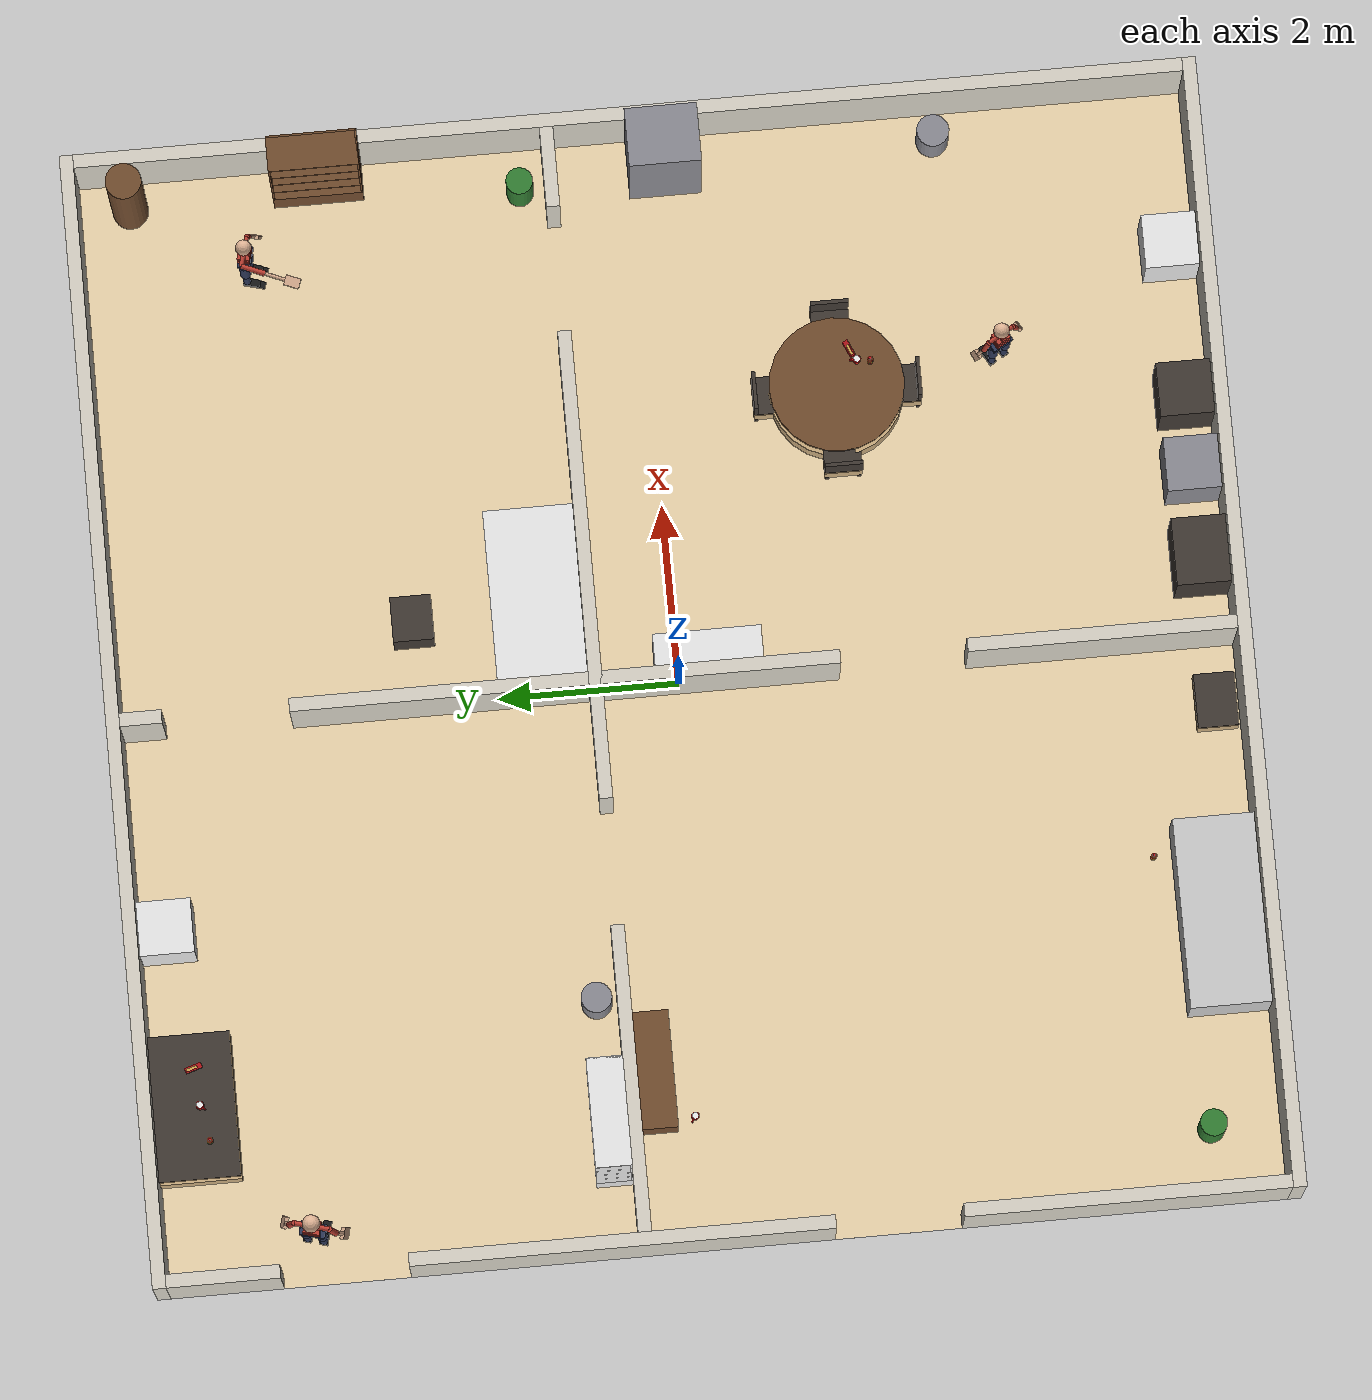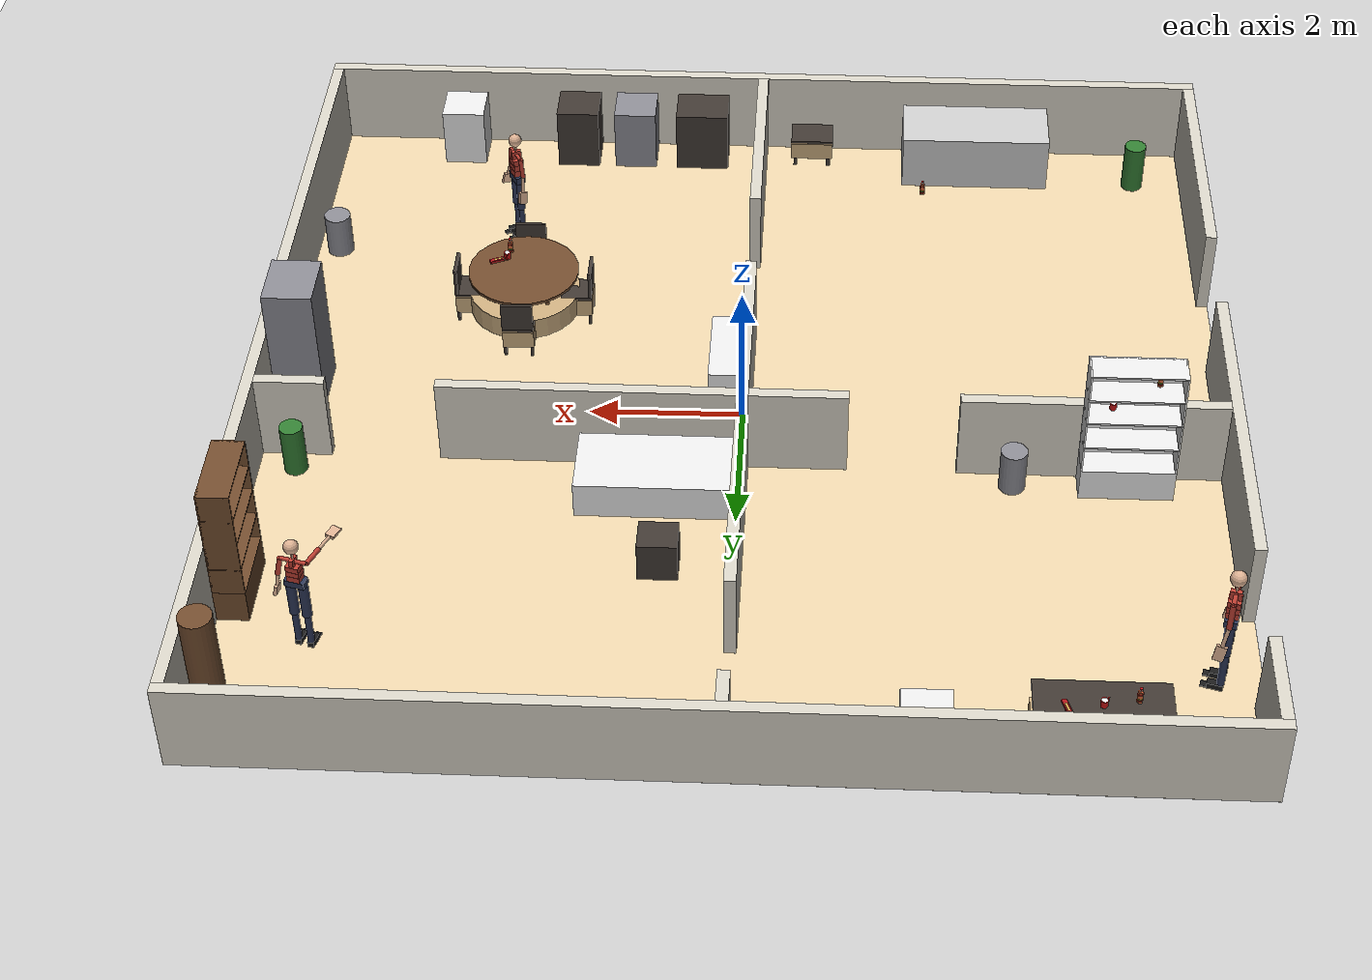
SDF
<?xml version="1.0"?>
<sdf version="1.6">
  <world name="robocup_casa">
    <include><uri>model://sun</uri></include>
    <include><uri>model://ground_plane</uri></include>
    <physics type="ode">
      <max_step_size>0.001</max_step_size>
      <real_time_factor>1.0</real_time_factor>
      <real_time_update_rate>1000</real_time_update_rate>
    </physics>
    <scene><shadows>false</shadows></scene>
    <gui><camera name="user_camera">
      <pose>0.00 -14.11 18.3 0 0.95 1.5708</pose></camera></gui>
    <model name="muros">
      <static>true</static>
      <link name="l0"><pose>0.000 -6.225 0.600 0 0 0.0000</pose>
        <collision name="c"><geometry><box><size>12.600 0.150 1.200</size></box></geometry></collision>
        <visual name="v"><geometry><box><size>12.600 0.150 1.200</size></box></geometry><material><ambient>0.85 0.83 0.78 1</ambient><diffuse>0.85 0.83 0.78 1</diffuse></material></visual>
      </link>
      <link name="l1"><pose>0.000 6.225 0.600 0 0 0.0000</pose>
        <collision name="c"><geometry><box><size>12.600 0.150 1.200</size></box></geometry></collision>
        <visual name="v"><geometry><box><size>12.600 0.150 1.200</size></box></geometry><material><ambient>0.85 0.83 0.78 1</ambient><diffuse>0.85 0.83 0.78 1</diffuse></material></visual>
      </link>
      <link name="l2"><pose>6.225 0.000 0.600 0 0 0.0000</pose>
        <collision name="c"><geometry><box><size>0.150 12.300 1.200</size></box></geometry></collision>
        <visual name="v"><geometry><box><size>0.150 12.300 1.200</size></box></geometry><material><ambient>0.85 0.83 0.78 1</ambient><diffuse>0.85 0.83 0.78 1</diffuse></material></visual>
      </link>
      <link name="l3"><pose>-6.225 -4.356 0.600 0 0 0.0000</pose>
        <collision name="c"><geometry><box><size>0.150 3.588 1.200</size></box></geometry></collision>
        <visual name="v"><geometry><box><size>0.150 3.588 1.200</size></box></geometry><material><ambient>0.85 0.83 0.78 1</ambient><diffuse>0.85 0.83 0.78 1</diffuse></material></visual>
      </link>
      <link name="l4"><pose>-6.225 1.169 0.600 0 0 0.0000</pose>
        <collision name="c"><geometry><box><size>0.150 4.662 1.200</size></box></geometry></collision>
        <visual name="v"><geometry><box><size>0.150 4.662 1.200</size></box></geometry><material><ambient>0.85 0.83 0.78 1</ambient><diffuse>0.85 0.83 0.78 1</diffuse></material></visual>
      </link>
      <link name="l5"><pose>-6.225 5.525 0.600 0 0 0.0000</pose>
        <collision name="c"><geometry><box><size>0.150 1.250 1.200</size></box></geometry></collision>
        <visual name="v"><geometry><box><size>0.150 1.250 1.200</size></box></geometry><material><ambient>0.85 0.83 0.78 1</ambient><diffuse>0.85 0.83 0.78 1</diffuse></material></visual>
      </link>
      <link name="l6"><pose>-0.035 -4.664 0.600 0 0 0.0000</pose>
        <collision name="c"><geometry><box><size>0.150 2.972 1.200</size></box></geometry></collision>
        <visual name="v"><geometry><box><size>0.150 2.972 1.200</size></box></geometry><material><ambient>0.85 0.83 0.78 1</ambient><diffuse>0.85 0.83 0.78 1</diffuse></material></visual>
      </link>
      <link name="l7"><pose>-0.035 1.253 0.600 0 0 0.0000</pose>
        <collision name="c"><geometry><box><size>0.150 6.062 1.200</size></box></geometry></collision>
        <visual name="v"><geometry><box><size>0.150 6.062 1.200</size></box></geometry><material><ambient>0.85 0.83 0.78 1</ambient><diffuse>0.85 0.83 0.78 1</diffuse></material></visual>
      </link>
      <link name="l8"><pose>-0.035 5.917 0.600 0 0 0.0000</pose>
        <collision name="c"><geometry><box><size>0.150 0.466 1.200</size></box></geometry></collision>
        <visual name="v"><geometry><box><size>0.150 0.466 1.200</size></box></geometry><material><ambient>0.85 0.83 0.78 1</ambient><diffuse>0.85 0.83 0.78 1</diffuse></material></visual>
      </link>
      <link name="l9"><pose>-4.461 0.917 0.600 0 0 0.0000</pose>
        <collision name="c"><geometry><box><size>3.378 0.150 1.200</size></box></geometry></collision>
        <visual name="v"><geometry><box><size>3.378 0.150 1.200</size></box></geometry><material><ambient>0.85 0.83 0.78 1</ambient><diffuse>0.85 0.83 0.78 1</diffuse></material></visual>
      </link>
      <link name="l10"><pose>1.239 0.917 0.600 0 0 0.0000</pose>
        <collision name="c"><geometry><box><size>5.222 0.150 1.200</size></box></geometry></collision>
        <visual name="v"><geometry><box><size>5.222 0.150 1.200</size></box></geometry><material><ambient>0.85 0.83 0.78 1</ambient><diffuse>0.85 0.83 0.78 1</diffuse></material></visual>
      </link>
      <link name="l11"><pose>5.700 0.917 0.600 0 0 0.0000</pose>
        <collision name="c"><geometry><box><size>0.900 0.150 1.200</size></box></geometry></collision>
        <visual name="v"><geometry><box><size>0.900 0.150 1.200</size></box></geometry><material><ambient>0.85 0.83 0.78 1</ambient><diffuse>0.85 0.83 0.78 1</diffuse></material></visual>
      </link>
    </model>
    <model name="piso_casa">
      <static>true</static>
      <link name="l"><pose>0.000 0.000 0.0005 0 0 0</pose>
        <visual name="v"><geometry><box><size>12.6 12.6 0.001</size></box></geometry><material><ambient>0.93 0.84 0.68 1</ambient><diffuse>0.93 0.84 0.68 1</diffuse></material></visual>
      </link>
    </model>
    <model name="laundry_table">
      <static>true</static>
      <link name="l0"><pose>-4.298 5.700 0.300 0 0 0.0000</pose>
        <collision name="c"><geometry><box><size>1.600 0.900 0.300</size></box></geometry></collision>
        <visual name="v"><geometry><box><size>1.600 0.900 0.300</size></box></geometry><material><ambient>0.80 0.68 0.50 1</ambient><diffuse>0.80 0.68 0.50 1</diffuse></material></visual>
      </link>
      <link name="l1"><pose>-4.298 5.700 0.730 0 0 0.0000</pose>
        <collision name="c"><geometry><box><size>1.600 0.900 0.040</size></box></geometry></collision>
        <visual name="v"><geometry><box><size>1.600 0.900 0.040</size></box></geometry><material><ambient>0.25 0.22 0.20 1</ambient><diffuse>0.25 0.22 0.20 1</diffuse></material></visual>
      </link>
      <link name="l2"><pose>-5.038 5.310 0.355 0 0 0.0000</pose>
        <collision name="c"><geometry><box><size>0.050 0.050 0.710</size></box></geometry></collision>
        <visual name="v"><geometry><box><size>0.050 0.050 0.710</size></box></geometry><material><ambient>0.25 0.22 0.20 1</ambient><diffuse>0.25 0.22 0.20 1</diffuse></material></visual>
      </link>
      <link name="l3"><pose>-5.038 6.090 0.355 0 0 0.0000</pose>
        <collision name="c"><geometry><box><size>0.050 0.050 0.710</size></box></geometry></collision>
        <visual name="v"><geometry><box><size>0.050 0.050 0.710</size></box></geometry><material><ambient>0.25 0.22 0.20 1</ambient><diffuse>0.25 0.22 0.20 1</diffuse></material></visual>
      </link>
      <link name="l4"><pose>-3.558 5.310 0.355 0 0 0.0000</pose>
        <collision name="c"><geometry><box><size>0.050 0.050 0.710</size></box></geometry></collision>
        <visual name="v"><geometry><box><size>0.050 0.050 0.710</size></box></geometry><material><ambient>0.25 0.22 0.20 1</ambient><diffuse>0.25 0.22 0.20 1</diffuse></material></visual>
      </link>
      <link name="l5"><pose>-3.558 6.090 0.355 0 0 0.0000</pose>
        <collision name="c"><geometry><box><size>0.050 0.050 0.710</size></box></geometry></collision>
        <visual name="v"><geometry><box><size>0.050 0.050 0.710</size></box></geometry><material><ambient>0.25 0.22 0.20 1</ambient><diffuse>0.25 0.22 0.20 1</diffuse></material></visual>
      </link>
    </model>
    <model name="washing_machine">
      <static>true</static>
      <link name="l0"><pose>-2.310 5.850 0.425 0 0 0.0000</pose>
        <collision name="c"><geometry><box><size>0.600 0.600 0.850</size></box></geometry></collision>
        <visual name="v"><geometry><box><size>0.600 0.600 0.850</size></box></geometry><material><ambient>0.92 0.92 0.92 1</ambient><diffuse>0.92 0.92 0.92 1</diffuse></material></visual>
      </link>
    </model>
    <model name="shelf">
      <static>true</static>
      <link name="l0"><pose>-4.900 1.192 0.225 0 0 0.0000</pose>
        <collision name="c"><geometry><box><size>1.200 0.400 0.450</size></box></geometry></collision>
        <visual name="v"><geometry><box><size>1.200 0.400 0.450</size></box></geometry><material><ambient>0.92 0.92 0.92 1</ambient><diffuse>0.92 0.92 0.92 1</diffuse></material></visual>
      </link>
      <link name="l1"><pose>-4.900 1.002 1.225 0 0 0.0000</pose>
        <collision name="c"><geometry><box><size>1.200 0.020 1.550</size></box></geometry></collision>
        <visual name="v"><geometry><box><size>1.200 0.020 1.550</size></box></geometry><material><ambient>0.92 0.92 0.92 1</ambient><diffuse>0.92 0.92 0.92 1</diffuse></material></visual>
      </link>
      <link name="l2"><pose>-5.490 1.192 1.225 0 0 0.0000</pose>
        <collision name="c"><geometry><box><size>0.020 0.400 1.550</size></box></geometry></collision>
        <visual name="v"><geometry><box><size>0.020 0.400 1.550</size></box></geometry><material><ambient>0.92 0.92 0.92 1</ambient><diffuse>0.92 0.92 0.92 1</diffuse></material></visual>
      </link>
      <link name="l3"><pose>-4.310 1.192 1.225 0 0 0.0000</pose>
        <collision name="c"><geometry><box><size>0.020 0.400 1.550</size></box></geometry></collision>
        <visual name="v"><geometry><box><size>0.020 0.400 1.550</size></box></geometry><material><ambient>0.92 0.92 0.92 1</ambient><diffuse>0.92 0.92 0.92 1</diffuse></material></visual>
      </link>
      <link name="l4"><pose>-4.900 1.192 0.840 0 0 0.0000</pose>
        <collision name="c"><geometry><box><size>1.200 0.400 0.020</size></box></geometry></collision>
        <visual name="v"><geometry><box><size>1.200 0.400 0.020</size></box></geometry><material><ambient>0.92 0.92 0.92 1</ambient><diffuse>0.92 0.92 0.92 1</diffuse></material></visual>
      </link>
      <link name="l5"><pose>-4.900 1.192 1.240 0 0 0.0000</pose>
        <collision name="c"><geometry><box><size>1.200 0.400 0.020</size></box></geometry></collision>
        <visual name="v"><geometry><box><size>1.200 0.400 0.020</size></box></geometry><material><ambient>0.92 0.92 0.92 1</ambient><diffuse>0.92 0.92 0.92 1</diffuse></material></visual>
      </link>
      <link name="l6"><pose>-4.900 1.192 1.610 0 0 0.0000</pose>
        <collision name="c"><geometry><box><size>1.200 0.400 0.020</size></box></geometry></collision>
        <visual name="v"><geometry><box><size>1.200 0.400 0.020</size></box></geometry><material><ambient>0.92 0.92 0.92 1</ambient><diffuse>0.92 0.92 0.92 1</diffuse></material></visual>
      </link>
      <link name="l7"><pose>-4.900 1.192 1.990 0 0 0.0000</pose>
        <collision name="c"><geometry><box><size>1.200 0.400 0.020</size></box></geometry></collision>
        <visual name="v"><geometry><box><size>1.200 0.400 0.020</size></box></geometry><material><ambient>0.92 0.92 0.92 1</ambient><diffuse>0.92 0.92 0.92 1</diffuse></material></visual>
      </link>
    </model>
    <model name="laundry_trash_bin">
      <static>true</static>
      <link name="l0"><pose>-3.472 1.212 0.300 0 0 0.0000</pose>
        <collision name="c"><geometry><cylinder><radius>0.170</radius><length>0.600</length></cylinder></geometry></collision>
        <visual name="v"><geometry><cylinder><radius>0.170</radius><length>0.600</length></cylinder></geometry><material><ambient>0.55 0.55 0.58 1</ambient><diffuse>0.55 0.55 0.58 1</diffuse></material></visual>
      </link>
    </model>
    <model name="bed">
      <static>true</static>
      <link name="l0"><pose>1.040 1.492 0.250 0 0 0.0000</pose>
        <collision name="c"><geometry><box><size>2.000 1.000 0.500</size></box></geometry></collision>
        <visual name="v"><geometry><box><size>2.000 1.000 0.500</size></box></geometry><material><ambient>0.92 0.92 0.92 1</ambient><diffuse>0.92 0.92 0.92 1</diffuse></material></visual>
      </link>
    </model>
    <model name="bedside_table">
      <static>true</static>
      <link name="l0"><pose>0.910 2.870 0.275 0 0 0.0000</pose>
        <collision name="c"><geometry><box><size>0.500 0.450 0.550</size></box></geometry></collision>
        <visual name="v"><geometry><box><size>0.500 0.450 0.550</size></box></geometry><material><ambient>0.25 0.22 0.20 1</ambient><diffuse>0.25 0.22 0.20 1</diffuse></material></visual>
      </link>
    </model>
    <model name="coat_rack">
      <static>true</static>
      <link name="l0"><pose>5.850 5.600 0.850 0 0 0.0000</pose>
        <collision name="c"><geometry><cylinder><radius>0.200</radius><length>1.700</length></cylinder></geometry></collision>
        <visual name="v"><geometry><cylinder><radius>0.200</radius><length>1.700</length></cylinder></geometry><material><ambient>0.45 0.30 0.18 1</ambient><diffuse>0.45 0.30 0.18 1</diffuse></material></visual>
      </link>
    </model>
    <model name="bookshelf">
      <static>true</static>
      <link name="l0"><pose>5.950 3.500 0.225 0 0 0.0000</pose>
        <collision name="c"><geometry><box><size>0.400 1.000 0.450</size></box></geometry></collision>
        <visual name="v"><geometry><box><size>0.400 1.000 0.450</size></box></geometry><material><ambient>0.45 0.30 0.18 1</ambient><diffuse>0.45 0.30 0.18 1</diffuse></material></visual>
      </link>
      <link name="l1"><pose>6.140 3.500 1.225 0 0 0.0000</pose>
        <collision name="c"><geometry><box><size>0.020 1.000 1.550</size></box></geometry></collision>
        <visual name="v"><geometry><box><size>0.020 1.000 1.550</size></box></geometry><material><ambient>0.45 0.30 0.18 1</ambient><diffuse>0.45 0.30 0.18 1</diffuse></material></visual>
      </link>
      <link name="l2"><pose>5.950 3.010 1.225 0 0 0.0000</pose>
        <collision name="c"><geometry><box><size>0.400 0.020 1.550</size></box></geometry></collision>
        <visual name="v"><geometry><box><size>0.400 0.020 1.550</size></box></geometry><material><ambient>0.45 0.30 0.18 1</ambient><diffuse>0.45 0.30 0.18 1</diffuse></material></visual>
      </link>
      <link name="l3"><pose>5.950 3.990 1.225 0 0 0.0000</pose>
        <collision name="c"><geometry><box><size>0.400 0.020 1.550</size></box></geometry></collision>
        <visual name="v"><geometry><box><size>0.400 0.020 1.550</size></box></geometry><material><ambient>0.45 0.30 0.18 1</ambient><diffuse>0.45 0.30 0.18 1</diffuse></material></visual>
      </link>
      <link name="l4"><pose>5.950 3.500 0.840 0 0 0.0000</pose>
        <collision name="c"><geometry><box><size>0.400 1.000 0.020</size></box></geometry></collision>
        <visual name="v"><geometry><box><size>0.400 1.000 0.020</size></box></geometry><material><ambient>0.45 0.30 0.18 1</ambient><diffuse>0.45 0.30 0.18 1</diffuse></material></visual>
      </link>
      <link name="l5"><pose>5.950 3.500 1.240 0 0 0.0000</pose>
        <collision name="c"><geometry><box><size>0.400 1.000 0.020</size></box></geometry></collision>
        <visual name="v"><geometry><box><size>0.400 1.000 0.020</size></box></geometry><material><ambient>0.45 0.30 0.18 1</ambient><diffuse>0.45 0.30 0.18 1</diffuse></material></visual>
      </link>
      <link name="l6"><pose>5.950 3.500 1.610 0 0 0.0000</pose>
        <collision name="c"><geometry><box><size>0.400 1.000 0.020</size></box></geometry></collision>
        <visual name="v"><geometry><box><size>0.400 1.000 0.020</size></box></geometry><material><ambient>0.45 0.30 0.18 1</ambient><diffuse>0.45 0.30 0.18 1</diffuse></material></visual>
      </link>
      <link name="l7"><pose>5.950 3.500 1.990 0 0 0.0000</pose>
        <collision name="c"><geometry><box><size>0.400 1.000 0.020</size></box></geometry></collision>
        <visual name="v"><geometry><box><size>0.400 1.000 0.020</size></box></geometry><material><ambient>0.45 0.30 0.18 1</ambient><diffuse>0.45 0.30 0.18 1</diffuse></material></visual>
      </link>
    </model>
    <model name="planta_bedroom">
      <static>true</static>
      <link name="l0"><pose>5.670 1.262 0.350 0 0 0.0000</pose>
        <collision name="c"><geometry><cylinder><radius>0.150</radius><length>0.700</length></cylinder></geometry></collision>
        <visual name="v"><geometry><cylinder><radius>0.150</radius><length>0.700</length></cylinder></geometry><material><ambient>0.20 0.50 0.20 1</ambient><diffuse>0.20 0.50 0.20 1</diffuse></material></visual>
      </link>
    </model>
    <model name="tv_stand">
      <static>true</static>
      <link name="l0"><pose>-4.312 0.642 0.250 0 0 0.0000</pose>
        <collision name="c"><geometry><box><size>1.300 0.400 0.500</size></box></geometry></collision>
        <visual name="v"><geometry><box><size>1.300 0.400 0.500</size></box></geometry><material><ambient>0.45 0.30 0.18 1</ambient><diffuse>0.45 0.30 0.18 1</diffuse></material></visual>
      </link>
    </model>
    <model name="sofa">
      <static>true</static>
      <link name="l0"><pose>-3.150 -5.700 0.400 0 0 0.0000</pose>
        <collision name="c"><geometry><box><size>2.100 0.900 0.800</size></box></geometry></collision>
        <visual name="v"><geometry><box><size>2.100 0.900 0.800</size></box></geometry><material><ambient>0.80 0.80 0.80 1</ambient><diffuse>0.80 0.80 0.80 1</diffuse></material></visual>
      </link>
    </model>
    <model name="coffee_table">
      <static>true</static>
      <link name="l0"><pose>-0.770 -5.880 0.275 0 0 0.0000</pose>
        <collision name="c"><geometry><box><size>0.600 0.450 0.250</size></box></geometry></collision>
        <visual name="v"><geometry><box><size>0.600 0.450 0.250</size></box></geometry><material><ambient>0.80 0.68 0.50 1</ambient><diffuse>0.80 0.68 0.50 1</diffuse></material></visual>
      </link>
      <link name="l1"><pose>-0.770 -5.880 0.430 0 0 0.0000</pose>
        <collision name="c"><geometry><box><size>0.600 0.450 0.040</size></box></geometry></collision>
        <visual name="v"><geometry><box><size>0.600 0.450 0.040</size></box></geometry><material><ambient>0.25 0.22 0.20 1</ambient><diffuse>0.25 0.22 0.20 1</diffuse></material></visual>
      </link>
      <link name="l2"><pose>-1.010 -6.045 0.205 0 0 0.0000</pose>
        <collision name="c"><geometry><box><size>0.050 0.050 0.410</size></box></geometry></collision>
        <visual name="v"><geometry><box><size>0.050 0.050 0.410</size></box></geometry><material><ambient>0.25 0.22 0.20 1</ambient><diffuse>0.25 0.22 0.20 1</diffuse></material></visual>
      </link>
      <link name="l3"><pose>-1.010 -5.715 0.205 0 0 0.0000</pose>
        <collision name="c"><geometry><box><size>0.050 0.050 0.410</size></box></geometry></collision>
        <visual name="v"><geometry><box><size>0.050 0.050 0.410</size></box></geometry><material><ambient>0.25 0.22 0.20 1</ambient><diffuse>0.25 0.22 0.20 1</diffuse></material></visual>
      </link>
      <link name="l4"><pose>-0.530 -6.045 0.205 0 0 0.0000</pose>
        <collision name="c"><geometry><box><size>0.050 0.050 0.410</size></box></geometry></collision>
        <visual name="v"><geometry><box><size>0.050 0.050 0.410</size></box></geometry><material><ambient>0.25 0.22 0.20 1</ambient><diffuse>0.25 0.22 0.20 1</diffuse></material></visual>
      </link>
      <link name="l5"><pose>-0.530 -5.715 0.205 0 0 0.0000</pose>
        <collision name="c"><geometry><box><size>0.050 0.050 0.410</size></box></geometry></collision>
        <visual name="v"><geometry><box><size>0.050 0.050 0.410</size></box></geometry><material><ambient>0.25 0.22 0.20 1</ambient><diffuse>0.25 0.22 0.20 1</diffuse></material></visual>
      </link>
    </model>
    <model name="planta_living">
      <static>true</static>
      <link name="l0"><pose>-5.460 -5.390 0.350 0 0 0.0000</pose>
        <collision name="c"><geometry><cylinder><radius>0.150</radius><length>0.700</length></cylinder></geometry></collision>
        <visual name="v"><geometry><cylinder><radius>0.150</radius><length>0.700</length></cylinder></geometry><material><ambient>0.20 0.50 0.20 1</ambient><diffuse>0.20 0.50 0.20 1</diffuse></material></visual>
      </link>
    </model>
    <model name="cabinet">
      <static>true</static>
      <link name="l0"><pose>0.240 -0.350 0.450 0 0 0.0000</pose>
        <collision name="c"><geometry><box><size>0.400 1.200 0.900</size></box></geometry></collision>
        <visual name="v"><geometry><box><size>0.400 1.200 0.900</size></box></geometry><material><ambient>0.92 0.92 0.92 1</ambient><diffuse>0.92 0.92 0.92 1</diffuse></material></visual>
      </link>
    </model>
    <model name="refrigerator">
      <static>true</static>
      <link name="l0"><pose>5.825 -0.350 0.900 0 0 0.0000</pose>
        <collision name="c"><geometry><box><size>0.650 0.800 1.800</size></box></geometry></collision>
        <visual name="v"><geometry><box><size>0.650 0.800 1.800</size></box></geometry><material><ambient>0.55 0.55 0.58 1</ambient><diffuse>0.55 0.55 0.58 1</diffuse></material></visual>
      </link>
    </model>
    <model name="kitchen_trash_bin">
      <static>true</static>
      <link name="l0"><pose>5.850 -3.360 0.300 0 0 0.0000</pose>
        <collision name="c"><geometry><cylinder><radius>0.180</radius><length>0.600</length></cylinder></geometry></collision>
        <visual name="v"><geometry><cylinder><radius>0.180</radius><length>0.600</length></cylinder></geometry><material><ambient>0.55 0.55 0.58 1</ambient><diffuse>0.55 0.55 0.58 1</diffuse></material></visual>
      </link>
    </model>
    <model name="dinner_table">
      <static>true</static>
      <link name="l0"><pose>3.066 -2.030 0.300 0 0 0.0000</pose>
        <collision name="c"><geometry><cylinder><radius>0.750</radius><length>0.300</length></cylinder></geometry></collision>
        <visual name="v"><geometry><cylinder><radius>0.750</radius><length>0.300</length></cylinder></geometry><material><ambient>0.80 0.68 0.50 1</ambient><diffuse>0.80 0.68 0.50 1</diffuse></material></visual>
      </link>
      <link name="l1"><pose>3.066 -2.030 0.730 0 0 0.0000</pose>
        <collision name="c"><geometry><cylinder><radius>0.750</radius><length>0.040</length></cylinder></geometry></collision>
        <visual name="v"><geometry><cylinder><radius>0.750</radius><length>0.040</length></cylinder></geometry><material><ambient>0.45 0.30 0.18 1</ambient><diffuse>0.45 0.30 0.18 1</diffuse></material></visual>
      </link>
      <link name="l2"><pose>2.721 -2.375 0.355 0 0 0.0000</pose>
        <collision name="c"><geometry><box><size>0.050 0.050 0.710</size></box></geometry></collision>
        <visual name="v"><geometry><box><size>0.050 0.050 0.710</size></box></geometry><material><ambient>0.45 0.30 0.18 1</ambient><diffuse>0.45 0.30 0.18 1</diffuse></material></visual>
      </link>
      <link name="l3"><pose>2.721 -1.685 0.355 0 0 0.0000</pose>
        <collision name="c"><geometry><box><size>0.050 0.050 0.710</size></box></geometry></collision>
        <visual name="v"><geometry><box><size>0.050 0.050 0.710</size></box></geometry><material><ambient>0.45 0.30 0.18 1</ambient><diffuse>0.45 0.30 0.18 1</diffuse></material></visual>
      </link>
      <link name="l4"><pose>3.411 -2.375 0.355 0 0 0.0000</pose>
        <collision name="c"><geometry><box><size>0.050 0.050 0.710</size></box></geometry></collision>
        <visual name="v"><geometry><box><size>0.050 0.050 0.710</size></box></geometry><material><ambient>0.45 0.30 0.18 1</ambient><diffuse>0.45 0.30 0.18 1</diffuse></material></visual>
      </link>
      <link name="l5"><pose>3.411 -1.685 0.355 0 0 0.0000</pose>
        <collision name="c"><geometry><box><size>0.050 0.050 0.710</size></box></geometry></collision>
        <visual name="v"><geometry><box><size>0.050 0.050 0.710</size></box></geometry><material><ambient>0.45 0.30 0.18 1</ambient><diffuse>0.45 0.30 0.18 1</diffuse></material></visual>
      </link>
    </model>
    <model name="counter">
      <static>true</static>
      <link name="l0"><pose>0.840 -5.850 0.450 0 0 0.0000</pose>
        <collision name="c"><geometry><box><size>0.750 0.600 0.900</size></box></geometry></collision>
        <visual name="v"><geometry><box><size>0.750 0.600 0.900</size></box></geometry><material><ambient>0.25 0.22 0.20 1</ambient><diffuse>0.25 0.22 0.20 1</diffuse></material></visual>
      </link>
    </model>
    <model name="sink">
      <static>true</static>
      <link name="l0"><pose>1.820 -5.850 0.450 0 0 0.0000</pose>
        <collision name="c"><geometry><box><size>0.600 0.600 0.900</size></box></geometry></collision>
        <visual name="v"><geometry><box><size>0.600 0.600 0.900</size></box></geometry><material><ambient>0.55 0.55 0.58 1</ambient><diffuse>0.55 0.55 0.58 1</diffuse></material></visual>
      </link>
    </model>
    <model name="cooking_table">
      <static>true</static>
      <link name="l0"><pose>2.660 -5.850 0.450 0 0 0.0000</pose>
        <collision name="c"><geometry><box><size>0.600 0.600 0.900</size></box></geometry></collision>
        <visual name="v"><geometry><box><size>0.600 0.600 0.900</size></box></geometry><material><ambient>0.25 0.22 0.20 1</ambient><diffuse>0.25 0.22 0.20 1</diffuse></material></visual>
      </link>
    </model>
    <model name="dishwasher">
      <static>true</static>
      <link name="l0"><pose>4.340 -5.850 0.425 0 0 0.0000</pose>
        <collision name="c"><geometry><box><size>0.600 0.600 0.850</size></box></geometry></collision>
        <visual name="v"><geometry><box><size>0.600 0.600 0.850</size></box></geometry><material><ambient>0.92 0.92 0.92 1</ambient><diffuse>0.92 0.92 0.92 1</diffuse></material></visual>
      </link>
    </model>
    <model name="silla_n">
      <static>true</static>
      <link name="l0"><pose>3.066 -1.310 0.275 0 0 -1.5708</pose>
        <collision name="c"><geometry><box><size>0.420 0.420 0.250</size></box></geometry></collision>
        <visual name="v"><geometry><box><size>0.420 0.420 0.250</size></box></geometry><material><ambient>0.80 0.68 0.50 1</ambient><diffuse>0.80 0.68 0.50 1</diffuse></material></visual>
      </link>
      <link name="l1"><pose>3.066 -1.310 0.430 0 0 -1.5708</pose>
        <collision name="c"><geometry><box><size>0.420 0.420 0.040</size></box></geometry></collision>
        <visual name="v"><geometry><box><size>0.420 0.420 0.040</size></box></geometry><material><ambient>0.25 0.22 0.20 1</ambient><diffuse>0.25 0.22 0.20 1</diffuse></material></visual>
      </link>
      <link name="l2"><pose>2.886 -1.130 0.205 0 0 -1.5708</pose>
        <collision name="c"><geometry><box><size>0.040 0.040 0.410</size></box></geometry></collision>
        <visual name="v"><geometry><box><size>0.040 0.040 0.410</size></box></geometry><material><ambient>0.25 0.22 0.20 1</ambient><diffuse>0.25 0.22 0.20 1</diffuse></material></visual>
      </link>
      <link name="l3"><pose>3.246 -1.130 0.205 0 0 -1.5708</pose>
        <collision name="c"><geometry><box><size>0.040 0.040 0.410</size></box></geometry></collision>
        <visual name="v"><geometry><box><size>0.040 0.040 0.410</size></box></geometry><material><ambient>0.25 0.22 0.20 1</ambient><diffuse>0.25 0.22 0.20 1</diffuse></material></visual>
      </link>
      <link name="l4"><pose>2.886 -1.490 0.205 0 0 -1.5708</pose>
        <collision name="c"><geometry><box><size>0.040 0.040 0.410</size></box></geometry></collision>
        <visual name="v"><geometry><box><size>0.040 0.040 0.410</size></box></geometry><material><ambient>0.25 0.22 0.20 1</ambient><diffuse>0.25 0.22 0.20 1</diffuse></material></visual>
      </link>
      <link name="l5"><pose>3.246 -1.490 0.205 0 0 -1.5708</pose>
        <collision name="c"><geometry><box><size>0.040 0.040 0.410</size></box></geometry></collision>
        <visual name="v"><geometry><box><size>0.040 0.040 0.410</size></box></geometry><material><ambient>0.25 0.22 0.20 1</ambient><diffuse>0.25 0.22 0.20 1</diffuse></material></visual>
      </link>
      <link name="l6"><pose>3.066 -1.120 0.650 0 0 -1.5708</pose>
        <collision name="c"><geometry><box><size>0.040 0.420 0.400</size></box></geometry></collision>
        <visual name="v"><geometry><box><size>0.040 0.420 0.400</size></box></geometry><material><ambient>0.25 0.22 0.20 1</ambient><diffuse>0.25 0.22 0.20 1</diffuse></material></visual>
      </link>
    </model>
    <model name="silla_s">
      <static>true</static>
      <link name="l0"><pose>3.066 -2.750 0.275 0 0 1.5708</pose>
        <collision name="c"><geometry><box><size>0.420 0.420 0.250</size></box></geometry></collision>
        <visual name="v"><geometry><box><size>0.420 0.420 0.250</size></box></geometry><material><ambient>0.80 0.68 0.50 1</ambient><diffuse>0.80 0.68 0.50 1</diffuse></material></visual>
      </link>
      <link name="l1"><pose>3.066 -2.750 0.430 0 0 1.5708</pose>
        <collision name="c"><geometry><box><size>0.420 0.420 0.040</size></box></geometry></collision>
        <visual name="v"><geometry><box><size>0.420 0.420 0.040</size></box></geometry><material><ambient>0.25 0.22 0.20 1</ambient><diffuse>0.25 0.22 0.20 1</diffuse></material></visual>
      </link>
      <link name="l2"><pose>3.246 -2.930 0.205 0 0 1.5708</pose>
        <collision name="c"><geometry><box><size>0.040 0.040 0.410</size></box></geometry></collision>
        <visual name="v"><geometry><box><size>0.040 0.040 0.410</size></box></geometry><material><ambient>0.25 0.22 0.20 1</ambient><diffuse>0.25 0.22 0.20 1</diffuse></material></visual>
      </link>
      <link name="l3"><pose>2.886 -2.930 0.205 0 0 1.5708</pose>
        <collision name="c"><geometry><box><size>0.040 0.040 0.410</size></box></geometry></collision>
        <visual name="v"><geometry><box><size>0.040 0.040 0.410</size></box></geometry><material><ambient>0.25 0.22 0.20 1</ambient><diffuse>0.25 0.22 0.20 1</diffuse></material></visual>
      </link>
      <link name="l4"><pose>3.246 -2.570 0.205 0 0 1.5708</pose>
        <collision name="c"><geometry><box><size>0.040 0.040 0.410</size></box></geometry></collision>
        <visual name="v"><geometry><box><size>0.040 0.040 0.410</size></box></geometry><material><ambient>0.25 0.22 0.20 1</ambient><diffuse>0.25 0.22 0.20 1</diffuse></material></visual>
      </link>
      <link name="l5"><pose>2.886 -2.570 0.205 0 0 1.5708</pose>
        <collision name="c"><geometry><box><size>0.040 0.040 0.410</size></box></geometry></collision>
        <visual name="v"><geometry><box><size>0.040 0.040 0.410</size></box></geometry><material><ambient>0.25 0.22 0.20 1</ambient><diffuse>0.25 0.22 0.20 1</diffuse></material></visual>
      </link>
      <link name="l6"><pose>3.066 -2.940 0.650 0 0 1.5708</pose>
        <collision name="c"><geometry><box><size>0.040 0.420 0.400</size></box></geometry></collision>
        <visual name="v"><geometry><box><size>0.040 0.420 0.400</size></box></geometry><material><ambient>0.25 0.22 0.20 1</ambient><diffuse>0.25 0.22 0.20 1</diffuse></material></visual>
      </link>
    </model>
    <model name="silla_o">
      <static>true</static>
      <link name="l0"><pose>2.346 -2.030 0.275 0 0 0.0000</pose>
        <collision name="c"><geometry><box><size>0.420 0.420 0.250</size></box></geometry></collision>
        <visual name="v"><geometry><box><size>0.420 0.420 0.250</size></box></geometry><material><ambient>0.80 0.68 0.50 1</ambient><diffuse>0.80 0.68 0.50 1</diffuse></material></visual>
      </link>
      <link name="l1"><pose>2.346 -2.030 0.430 0 0 0.0000</pose>
        <collision name="c"><geometry><box><size>0.420 0.420 0.040</size></box></geometry></collision>
        <visual name="v"><geometry><box><size>0.420 0.420 0.040</size></box></geometry><material><ambient>0.25 0.22 0.20 1</ambient><diffuse>0.25 0.22 0.20 1</diffuse></material></visual>
      </link>
      <link name="l2"><pose>2.166 -2.210 0.205 0 0 0.0000</pose>
        <collision name="c"><geometry><box><size>0.040 0.040 0.410</size></box></geometry></collision>
        <visual name="v"><geometry><box><size>0.040 0.040 0.410</size></box></geometry><material><ambient>0.25 0.22 0.20 1</ambient><diffuse>0.25 0.22 0.20 1</diffuse></material></visual>
      </link>
      <link name="l3"><pose>2.166 -1.850 0.205 0 0 0.0000</pose>
        <collision name="c"><geometry><box><size>0.040 0.040 0.410</size></box></geometry></collision>
        <visual name="v"><geometry><box><size>0.040 0.040 0.410</size></box></geometry><material><ambient>0.25 0.22 0.20 1</ambient><diffuse>0.25 0.22 0.20 1</diffuse></material></visual>
      </link>
      <link name="l4"><pose>2.526 -2.210 0.205 0 0 0.0000</pose>
        <collision name="c"><geometry><box><size>0.040 0.040 0.410</size></box></geometry></collision>
        <visual name="v"><geometry><box><size>0.040 0.040 0.410</size></box></geometry><material><ambient>0.25 0.22 0.20 1</ambient><diffuse>0.25 0.22 0.20 1</diffuse></material></visual>
      </link>
      <link name="l5"><pose>2.526 -1.850 0.205 0 0 0.0000</pose>
        <collision name="c"><geometry><box><size>0.040 0.040 0.410</size></box></geometry></collision>
        <visual name="v"><geometry><box><size>0.040 0.040 0.410</size></box></geometry><material><ambient>0.25 0.22 0.20 1</ambient><diffuse>0.25 0.22 0.20 1</diffuse></material></visual>
      </link>
      <link name="l6"><pose>2.156 -2.030 0.650 0 0 0.0000</pose>
        <collision name="c"><geometry><box><size>0.040 0.420 0.400</size></box></geometry></collision>
        <visual name="v"><geometry><box><size>0.040 0.420 0.400</size></box></geometry><material><ambient>0.25 0.22 0.20 1</ambient><diffuse>0.25 0.22 0.20 1</diffuse></material></visual>
      </link>
    </model>
    <model name="silla_e">
      <static>true</static>
      <link name="l0"><pose>3.786 -2.030 0.275 0 0 3.1416</pose>
        <collision name="c"><geometry><box><size>0.420 0.420 0.250</size></box></geometry></collision>
        <visual name="v"><geometry><box><size>0.420 0.420 0.250</size></box></geometry><material><ambient>0.80 0.68 0.50 1</ambient><diffuse>0.80 0.68 0.50 1</diffuse></material></visual>
      </link>
      <link name="l1"><pose>3.786 -2.030 0.430 0 0 3.1416</pose>
        <collision name="c"><geometry><box><size>0.420 0.420 0.040</size></box></geometry></collision>
        <visual name="v"><geometry><box><size>0.420 0.420 0.040</size></box></geometry><material><ambient>0.25 0.22 0.20 1</ambient><diffuse>0.25 0.22 0.20 1</diffuse></material></visual>
      </link>
      <link name="l2"><pose>3.966 -1.850 0.205 0 0 3.1416</pose>
        <collision name="c"><geometry><box><size>0.040 0.040 0.410</size></box></geometry></collision>
        <visual name="v"><geometry><box><size>0.040 0.040 0.410</size></box></geometry><material><ambient>0.25 0.22 0.20 1</ambient><diffuse>0.25 0.22 0.20 1</diffuse></material></visual>
      </link>
      <link name="l3"><pose>3.966 -2.210 0.205 0 0 3.1416</pose>
        <collision name="c"><geometry><box><size>0.040 0.040 0.410</size></box></geometry></collision>
        <visual name="v"><geometry><box><size>0.040 0.040 0.410</size></box></geometry><material><ambient>0.25 0.22 0.20 1</ambient><diffuse>0.25 0.22 0.20 1</diffuse></material></visual>
      </link>
      <link name="l4"><pose>3.606 -1.850 0.205 0 0 3.1416</pose>
        <collision name="c"><geometry><box><size>0.040 0.040 0.410</size></box></geometry></collision>
        <visual name="v"><geometry><box><size>0.040 0.040 0.410</size></box></geometry><material><ambient>0.25 0.22 0.20 1</ambient><diffuse>0.25 0.22 0.20 1</diffuse></material></visual>
      </link>
      <link name="l5"><pose>3.606 -2.210 0.205 0 0 3.1416</pose>
        <collision name="c"><geometry><box><size>0.040 0.040 0.410</size></box></geometry></collision>
        <visual name="v"><geometry><box><size>0.040 0.040 0.410</size></box></geometry><material><ambient>0.25 0.22 0.20 1</ambient><diffuse>0.25 0.22 0.20 1</diffuse></material></visual>
      </link>
      <link name="l6"><pose>3.976 -2.030 0.650 0 0 3.1416</pose>
        <collision name="c"><geometry><box><size>0.040 0.420 0.400</size></box></geometry></collision>
        <visual name="v"><geometry><box><size>0.040 0.420 0.400</size></box></geometry><material><ambient>0.25 0.22 0.20 1</ambient><diffuse>0.25 0.22 0.20 1</diffuse></material></visual>
      </link>
    </model>
    <model name="botella_laundry">
      <pose>-4.698 5.550 0.751 0 0 1.571</pose>
      <link name="link">
        <inertial><pose>0 0 0.1100 0 0 0</pose><mass>0.55</mass><inertia><ixx>2.368e-03</ixx><iyy>2.368e-03</iyy><izz>2.995e-04</izz><ixy>0</ixy><ixz>0</ixz><iyz>0</iyz></inertia></inertial>
        <collision name="c"><pose>0 0 0.1100 0 0 0</pose><geometry><cylinder><radius>0.0330</radius><length>0.2200</length></cylinder></geometry><surface><friction><ode><mu>1.0</mu><mu2>1.0</mu2></ode></friction></surface></collision>
        <visual name="v0"><pose>0 0 0.075 0 0 0</pose><geometry><cylinder><radius>0.0330</radius><length>0.1500</length></cylinder></geometry><transparency>0</transparency><material><ambient>0.86 0.40 0.22 1</ambient><diffuse>0.86 0.40 0.22 1</diffuse></material></visual>
        <visual name="v1"><pose>0 0 0.16 0 0 0</pose><geometry><cylinder><radius>0.0270</radius><length>0.0200</length></cylinder></geometry><transparency>0</transparency><material><ambient>0.86 0.40 0.22 1</ambient><diffuse>0.86 0.40 0.22 1</diffuse></material></visual>
        <visual name="v2"><pose>0 0 0.182 0 0 0</pose><geometry><cylinder><radius>0.0150</radius><length>0.0250</length></cylinder></geometry><transparency>0.4</transparency><material><ambient>0.75 0.78 0.80 1</ambient><diffuse>0.75 0.78 0.80 1</diffuse></material></visual>
        <visual name="v3"><pose>0 0 0.192 0 0 0</pose><geometry><cylinder><radius>0.0190</radius><length>0.0040</length></cylinder></geometry><transparency>0.2</transparency><material><ambient>0.75 0.78 0.80 1</ambient><diffuse>0.75 0.78 0.80 1</diffuse></material></visual>
        <visual name="v4"><pose>0 0 0.2075 0 0 0</pose><geometry><cylinder><radius>0.0160</radius><length>0.0250</length></cylinder></geometry><transparency>0</transparency><material><ambient>0.80 0.10 0.12 1</ambient><diffuse>0.80 0.10 0.12 1</diffuse></material></visual>
        <visual name="v5"><pose>0 0 0.13 0 0 0</pose><geometry><cylinder><radius>0.0340</radius><length>0.0120</length></cylinder></geometry><transparency>0</transparency><material><ambient>0.80 0.10 0.12 1</ambient><diffuse>0.80 0.10 0.12 1</diffuse></material></visual>
        <visual name="v6"><pose>0 0 0.0625 0 0 0</pose><geometry><cylinder><radius>0.0340</radius><length>0.0150</length></cylinder></geometry><transparency>0</transparency><material><ambient>0.85 0.75 0.20 1</ambient><diffuse>0.85 0.75 0.20 1</diffuse></material></visual>
        <visual name="v7"><pose>0 0 0.05 0 0 0</pose><geometry><cylinder><radius>0.0340</radius><length>0.0100</length></cylinder></geometry><transparency>0</transparency><material><ambient>0.30 0.60 0.25 1</ambient><diffuse>0.30 0.60 0.25 1</diffuse></material></visual>
        <visual name="v8"><pose>0 0 0.0375 0 0 0</pose><geometry><cylinder><radius>0.0340</radius><length>0.0150</length></cylinder></geometry><transparency>0</transparency><material><ambient>0.80 0.10 0.12 1</ambient><diffuse>0.80 0.10 0.12 1</diffuse></material></visual>
      </link>
    </model>
    <model name="taza_laundry">
      <pose>-4.298 5.630 0.751 0 0 -2.312</pose>
      <link name="link">
        <inertial><pose>0 0 0.0475 0 0 0</pose><mass>0.3</mass><inertia><ixx>3.643e-04</ixx><iyy>3.643e-04</iyy><izz>2.773e-04</izz><ixy>0</ixy><ixz>0</ixz><iyz>0</iyz></inertia></inertial>
        <collision name="c"><pose>0 0 0.0475 0 0 0</pose><geometry><cylinder><radius>0.0430</radius><length>0.0950</length></cylinder></geometry><surface><friction><ode><mu>1.0</mu><mu2>1.0</mu2></ode></friction></surface></collision>
        <visual name="v0"><pose>0 0 0.0475 0 0 0</pose><geometry><cylinder><radius>0.0430</radius><length>0.0950</length></cylinder></geometry><transparency>0</transparency><material><ambient>0.82 0.08 0.08 1</ambient><diffuse>0.82 0.08 0.08 1</diffuse></material></visual>
        <visual name="v1"><pose>0 0 0.0945 0 0 0</pose><geometry><cylinder><radius>0.0370</radius><length>0.0020</length></cylinder></geometry><transparency>0</transparency><material><ambient>0.95 0.95 0.95 1</ambient><diffuse>0.95 0.95 0.95 1</diffuse></material></visual>
        <visual name="v2"><pose>0.073 0 0.048 0 0 0</pose><geometry><box><size>0.0120 0.0140 0.0660</size></box></geometry><transparency>0</transparency><material><ambient>0.82 0.08 0.08 1</ambient><diffuse>0.82 0.08 0.08 1</diffuse></material></visual>
        <visual name="v3"><pose>0.058 0 0.075 0 0 0</pose><geometry><box><size>0.0320 0.0140 0.0120</size></box></geometry><transparency>0</transparency><material><ambient>0.82 0.08 0.08 1</ambient><diffuse>0.82 0.08 0.08 1</diffuse></material></visual>
        <visual name="v4"><pose>0.058 0 0.021 0 0 0</pose><geometry><box><size>0.0320 0.0140 0.0120</size></box></geometry><transparency>0</transparency><material><ambient>0.82 0.08 0.08 1</ambient><diffuse>0.82 0.08 0.08 1</diffuse></material></visual>
      </link>
    </model>
    <model name="galletas_laundry">
      <pose>-3.878 5.670 0.751 0 0 1.871</pose>
      <link name="link">
        <inertial><pose>0 0 0.0175 0 0 0</pose><mass>0.13</mass><inertia><ixx>5.491e-05</ixx><iyy>4.044e-04</iyy><izz>4.327e-04</izz><ixy>0</ixy><ixz>0</ixz><iyz>0</iyz></inertia></inertial>
        <collision name="c"><pose>0 0 0.0175 0 0 0</pose><geometry><box><size>0.1900 0.0620 0.0350</size></box></geometry><surface><friction><ode><mu>1.0</mu><mu2>1.0</mu2></ode></friction></surface></collision>
        <visual name="v0"><pose>0 0 0.0175 0 0 0</pose><geometry><box><size>0.1900 0.0620 0.0350</size></box></geometry><transparency>0</transparency><material><ambient>0.70 0.08 0.10 1</ambient><diffuse>0.70 0.08 0.10 1</diffuse></material></visual>
        <visual name="v1"><pose>0.02 0 0.0355 0 0 0</pose><geometry><box><size>0.1200 0.0300 0.0010</size></box></geometry><transparency>0</transparency><material><ambient>0.85 0.65 0.30 1</ambient><diffuse>0.85 0.65 0.30 1</diffuse></material></visual>
      </link>
    </model>
    <model name="taza_comedor">
      <pose>3.313 -2.277 0.751 0 0 1.556</pose>
      <link name="link">
        <inertial><pose>0 0 0.0475 0 0 0</pose><mass>0.3</mass><inertia><ixx>3.643e-04</ixx><iyy>3.643e-04</iyy><izz>2.773e-04</izz><ixy>0</ixy><ixz>0</ixz><iyz>0</iyz></inertia></inertial>
        <collision name="c"><pose>0 0 0.0475 0 0 0</pose><geometry><cylinder><radius>0.0430</radius><length>0.0950</length></cylinder></geometry><surface><friction><ode><mu>1.0</mu><mu2>1.0</mu2></ode></friction></surface></collision>
        <visual name="v0"><pose>0 0 0.0475 0 0 0</pose><geometry><cylinder><radius>0.0430</radius><length>0.0950</length></cylinder></geometry><transparency>0</transparency><material><ambient>0.82 0.08 0.08 1</ambient><diffuse>0.82 0.08 0.08 1</diffuse></material></visual>
        <visual name="v1"><pose>0 0 0.0945 0 0 0</pose><geometry><cylinder><radius>0.0370</radius><length>0.0020</length></cylinder></geometry><transparency>0</transparency><material><ambient>0.95 0.95 0.95 1</ambient><diffuse>0.95 0.95 0.95 1</diffuse></material></visual>
        <visual name="v2"><pose>0.073 0 0.048 0 0 0</pose><geometry><box><size>0.0120 0.0140 0.0660</size></box></geometry><transparency>0</transparency><material><ambient>0.82 0.08 0.08 1</ambient><diffuse>0.82 0.08 0.08 1</diffuse></material></visual>
        <visual name="v3"><pose>0.058 0 0.075 0 0 0</pose><geometry><box><size>0.0320 0.0140 0.0120</size></box></geometry><transparency>0</transparency><material><ambient>0.82 0.08 0.08 1</ambient><diffuse>0.82 0.08 0.08 1</diffuse></material></visual>
        <visual name="v4"><pose>0.058 0 0.021 0 0 0</pose><geometry><box><size>0.0320 0.0140 0.0120</size></box></geometry><transparency>0</transparency><material><ambient>0.82 0.08 0.08 1</ambient><diffuse>0.82 0.08 0.08 1</diffuse></material></visual>
      </link>
    </model>
    <model name="botella_comedor">
      <pose>3.285 -2.419 0.751 0 0 2.356</pose>
      <link name="link">
        <inertial><pose>0 0 0.1100 0 0 0</pose><mass>0.55</mass><inertia><ixx>2.368e-03</ixx><iyy>2.368e-03</iyy><izz>2.995e-04</izz><ixy>0</ixy><ixz>0</ixz><iyz>0</iyz></inertia></inertial>
        <collision name="c"><pose>0 0 0.1100 0 0 0</pose><geometry><cylinder><radius>0.0330</radius><length>0.2200</length></cylinder></geometry><surface><friction><ode><mu>1.0</mu><mu2>1.0</mu2></ode></friction></surface></collision>
        <visual name="v0"><pose>0 0 0.075 0 0 0</pose><geometry><cylinder><radius>0.0330</radius><length>0.1500</length></cylinder></geometry><transparency>0</transparency><material><ambient>0.86 0.40 0.22 1</ambient><diffuse>0.86 0.40 0.22 1</diffuse></material></visual>
        <visual name="v1"><pose>0 0 0.16 0 0 0</pose><geometry><cylinder><radius>0.0270</radius><length>0.0200</length></cylinder></geometry><transparency>0</transparency><material><ambient>0.86 0.40 0.22 1</ambient><diffuse>0.86 0.40 0.22 1</diffuse></material></visual>
        <visual name="v2"><pose>0 0 0.182 0 0 0</pose><geometry><cylinder><radius>0.0150</radius><length>0.0250</length></cylinder></geometry><transparency>0.4</transparency><material><ambient>0.75 0.78 0.80 1</ambient><diffuse>0.75 0.78 0.80 1</diffuse></material></visual>
        <visual name="v3"><pose>0 0 0.192 0 0 0</pose><geometry><cylinder><radius>0.0190</radius><length>0.0040</length></cylinder></geometry><transparency>0.2</transparency><material><ambient>0.75 0.78 0.80 1</ambient><diffuse>0.75 0.78 0.80 1</diffuse></material></visual>
        <visual name="v4"><pose>0 0 0.2075 0 0 0</pose><geometry><cylinder><radius>0.0160</radius><length>0.0250</length></cylinder></geometry><transparency>0</transparency><material><ambient>0.80 0.10 0.12 1</ambient><diffuse>0.80 0.10 0.12 1</diffuse></material></visual>
        <visual name="v5"><pose>0 0 0.13 0 0 0</pose><geometry><cylinder><radius>0.0340</radius><length>0.0120</length></cylinder></geometry><transparency>0</transparency><material><ambient>0.80 0.10 0.12 1</ambient><diffuse>0.80 0.10 0.12 1</diffuse></material></visual>
        <visual name="v6"><pose>0 0 0.0625 0 0 0</pose><geometry><cylinder><radius>0.0340</radius><length>0.0150</length></cylinder></geometry><transparency>0</transparency><material><ambient>0.85 0.75 0.20 1</ambient><diffuse>0.85 0.75 0.20 1</diffuse></material></visual>
        <visual name="v7"><pose>0 0 0.05 0 0 0</pose><geometry><cylinder><radius>0.0340</radius><length>0.0100</length></cylinder></geometry><transparency>0</transparency><material><ambient>0.30 0.60 0.25 1</ambient><diffuse>0.30 0.60 0.25 1</diffuse></material></visual>
        <visual name="v8"><pose>0 0 0.0375 0 0 0</pose><geometry><cylinder><radius>0.0340</radius><length>0.0150</length></cylinder></geometry><transparency>0</transparency><material><ambient>0.80 0.10 0.12 1</ambient><diffuse>0.80 0.10 0.12 1</diffuse></material></visual>
      </link>
    </model>
    <model name="galletas_comedor">
      <pose>3.448 -2.200 0.751 0 0 -2.727</pose>
      <link name="link">
        <inertial><pose>0 0 0.0175 0 0 0</pose><mass>0.13</mass><inertia><ixx>5.491e-05</ixx><iyy>4.044e-04</iyy><izz>4.327e-04</izz><ixy>0</ixy><ixz>0</ixz><iyz>0</iyz></inertia></inertial>
        <collision name="c"><pose>0 0 0.0175 0 0 0</pose><geometry><box><size>0.1900 0.0620 0.0350</size></box></geometry><surface><friction><ode><mu>1.0</mu><mu2>1.0</mu2></ode></friction></surface></collision>
        <visual name="v0"><pose>0 0 0.0175 0 0 0</pose><geometry><box><size>0.1900 0.0620 0.0350</size></box></geometry><transparency>0</transparency><material><ambient>0.70 0.08 0.10 1</ambient><diffuse>0.70 0.08 0.10 1</diffuse></material></visual>
        <visual name="v1"><pose>0.02 0 0.0355 0 0 0</pose><geometry><box><size>0.1200 0.0300 0.0010</size></box></geometry><transparency>0</transparency><material><ambient>0.85 0.65 0.30 1</ambient><diffuse>0.85 0.65 0.30 1</diffuse></material></visual>
      </link>
    </model>
    <model name="taza_estante">
      <pose>-4.650 1.102 1.251 0 0 -1.571</pose>
      <link name="link">
        <inertial><pose>0 0 0.0475 0 0 0</pose><mass>0.3</mass><inertia><ixx>3.643e-04</ixx><iyy>3.643e-04</iyy><izz>2.773e-04</izz><ixy>0</ixy><ixz>0</ixz><iyz>0</iyz></inertia></inertial>
        <collision name="c"><pose>0 0 0.0475 0 0 0</pose><geometry><cylinder><radius>0.0430</radius><length>0.0950</length></cylinder></geometry><surface><friction><ode><mu>1.0</mu><mu2>1.0</mu2></ode></friction></surface></collision>
        <visual name="v0"><pose>0 0 0.0475 0 0 0</pose><geometry><cylinder><radius>0.0430</radius><length>0.0950</length></cylinder></geometry><transparency>0</transparency><material><ambient>0.82 0.08 0.08 1</ambient><diffuse>0.82 0.08 0.08 1</diffuse></material></visual>
        <visual name="v1"><pose>0 0 0.0945 0 0 0</pose><geometry><cylinder><radius>0.0370</radius><length>0.0020</length></cylinder></geometry><transparency>0</transparency><material><ambient>0.95 0.95 0.95 1</ambient><diffuse>0.95 0.95 0.95 1</diffuse></material></visual>
        <visual name="v2"><pose>0.073 0 0.048 0 0 0</pose><geometry><box><size>0.0120 0.0140 0.0660</size></box></geometry><transparency>0</transparency><material><ambient>0.82 0.08 0.08 1</ambient><diffuse>0.82 0.08 0.08 1</diffuse></material></visual>
        <visual name="v3"><pose>0.058 0 0.075 0 0 0</pose><geometry><box><size>0.0320 0.0140 0.0120</size></box></geometry><transparency>0</transparency><material><ambient>0.82 0.08 0.08 1</ambient><diffuse>0.82 0.08 0.08 1</diffuse></material></visual>
        <visual name="v4"><pose>0.058 0 0.021 0 0 0</pose><geometry><box><size>0.0320 0.0140 0.0120</size></box></geometry><transparency>0</transparency><material><ambient>0.82 0.08 0.08 1</ambient><diffuse>0.82 0.08 0.08 1</diffuse></material></visual>
      </link>
    </model>
    <model name="botella_estante">
      <pose>-5.200 1.072 1.621 0 0 -1.571</pose>
      <link name="link">
        <inertial><pose>0 0 0.1100 0 0 0</pose><mass>0.55</mass><inertia><ixx>2.368e-03</ixx><iyy>2.368e-03</iyy><izz>2.995e-04</izz><ixy>0</ixy><ixz>0</ixz><iyz>0</iyz></inertia></inertial>
        <collision name="c"><pose>0 0 0.1100 0 0 0</pose><geometry><cylinder><radius>0.0330</radius><length>0.2200</length></cylinder></geometry><surface><friction><ode><mu>1.0</mu><mu2>1.0</mu2></ode></friction></surface></collision>
        <visual name="v0"><pose>0 0 0.075 0 0 0</pose><geometry><cylinder><radius>0.0330</radius><length>0.1500</length></cylinder></geometry><transparency>0</transparency><material><ambient>0.86 0.40 0.22 1</ambient><diffuse>0.86 0.40 0.22 1</diffuse></material></visual>
        <visual name="v1"><pose>0 0 0.16 0 0 0</pose><geometry><cylinder><radius>0.0270</radius><length>0.0200</length></cylinder></geometry><transparency>0</transparency><material><ambient>0.86 0.40 0.22 1</ambient><diffuse>0.86 0.40 0.22 1</diffuse></material></visual>
        <visual name="v2"><pose>0 0 0.182 0 0 0</pose><geometry><cylinder><radius>0.0150</radius><length>0.0250</length></cylinder></geometry><transparency>0.4</transparency><material><ambient>0.75 0.78 0.80 1</ambient><diffuse>0.75 0.78 0.80 1</diffuse></material></visual>
        <visual name="v3"><pose>0 0 0.192 0 0 0</pose><geometry><cylinder><radius>0.0190</radius><length>0.0040</length></cylinder></geometry><transparency>0.2</transparency><material><ambient>0.75 0.78 0.80 1</ambient><diffuse>0.75 0.78 0.80 1</diffuse></material></visual>
        <visual name="v4"><pose>0 0 0.2075 0 0 0</pose><geometry><cylinder><radius>0.0160</radius><length>0.0250</length></cylinder></geometry><transparency>0</transparency><material><ambient>0.80 0.10 0.12 1</ambient><diffuse>0.80 0.10 0.12 1</diffuse></material></visual>
        <visual name="v5"><pose>0 0 0.13 0 0 0</pose><geometry><cylinder><radius>0.0340</radius><length>0.0120</length></cylinder></geometry><transparency>0</transparency><material><ambient>0.80 0.10 0.12 1</ambient><diffuse>0.80 0.10 0.12 1</diffuse></material></visual>
        <visual name="v6"><pose>0 0 0.0625 0 0 0</pose><geometry><cylinder><radius>0.0340</radius><length>0.0150</length></cylinder></geometry><transparency>0</transparency><material><ambient>0.85 0.75 0.20 1</ambient><diffuse>0.85 0.75 0.20 1</diffuse></material></visual>
        <visual name="v7"><pose>0 0 0.05 0 0 0</pose><geometry><cylinder><radius>0.0340</radius><length>0.0100</length></cylinder></geometry><transparency>0</transparency><material><ambient>0.30 0.60 0.25 1</ambient><diffuse>0.30 0.60 0.25 1</diffuse></material></visual>
        <visual name="v8"><pose>0 0 0.0375 0 0 0</pose><geometry><cylinder><radius>0.0340</radius><length>0.0150</length></cylinder></geometry><transparency>0</transparency><material><ambient>0.80 0.10 0.12 1</ambient><diffuse>0.80 0.10 0.12 1</diffuse></material></visual>
      </link>
    </model>
    <model name="galletas_librero">
      <pose>6.050 3.700 1.621 0 0 1.571</pose>
      <link name="link">
        <inertial><pose>0 0 0.0175 0 0 0</pose><mass>0.13</mass><inertia><ixx>5.491e-05</ixx><iyy>4.044e-04</iyy><izz>4.327e-04</izz><ixy>0</ixy><ixz>0</ixz><iyz>0</iyz></inertia></inertial>
        <collision name="c"><pose>0 0 0.0175 0 0 0</pose><geometry><box><size>0.1900 0.0620 0.0350</size></box></geometry><surface><friction><ode><mu>1.0</mu><mu2>1.0</mu2></ode></friction></surface></collision>
        <visual name="v0"><pose>0 0 0.0175 0 0 0</pose><geometry><box><size>0.1900 0.0620 0.0350</size></box></geometry><transparency>0</transparency><material><ambient>0.70 0.08 0.10 1</ambient><diffuse>0.70 0.08 0.10 1</diffuse></material></visual>
        <visual name="v1"><pose>0.02 0 0.0355 0 0 0</pose><geometry><box><size>0.1200 0.0300 0.0010</size></box></geometry><transparency>0</transparency><material><ambient>0.85 0.65 0.30 1</ambient><diffuse>0.85 0.65 0.30 1</diffuse></material></visual>
      </link>
    </model>
    <model name="botella_librero">
      <pose>6.070 3.250 0.851 0 0 0.000</pose>
      <link name="link">
        <inertial><pose>0 0 0.1100 0 0 0</pose><mass>0.55</mass><inertia><ixx>2.368e-03</ixx><iyy>2.368e-03</iyy><izz>2.995e-04</izz><ixy>0</ixy><ixz>0</ixz><iyz>0</iyz></inertia></inertial>
        <collision name="c"><pose>0 0 0.1100 0 0 0</pose><geometry><cylinder><radius>0.0330</radius><length>0.2200</length></cylinder></geometry><surface><friction><ode><mu>1.0</mu><mu2>1.0</mu2></ode></friction></surface></collision>
        <visual name="v0"><pose>0 0 0.075 0 0 0</pose><geometry><cylinder><radius>0.0330</radius><length>0.1500</length></cylinder></geometry><transparency>0</transparency><material><ambient>0.86 0.40 0.22 1</ambient><diffuse>0.86 0.40 0.22 1</diffuse></material></visual>
        <visual name="v1"><pose>0 0 0.16 0 0 0</pose><geometry><cylinder><radius>0.0270</radius><length>0.0200</length></cylinder></geometry><transparency>0</transparency><material><ambient>0.86 0.40 0.22 1</ambient><diffuse>0.86 0.40 0.22 1</diffuse></material></visual>
        <visual name="v2"><pose>0 0 0.182 0 0 0</pose><geometry><cylinder><radius>0.0150</radius><length>0.0250</length></cylinder></geometry><transparency>0.4</transparency><material><ambient>0.75 0.78 0.80 1</ambient><diffuse>0.75 0.78 0.80 1</diffuse></material></visual>
        <visual name="v3"><pose>0 0 0.192 0 0 0</pose><geometry><cylinder><radius>0.0190</radius><length>0.0040</length></cylinder></geometry><transparency>0.2</transparency><material><ambient>0.75 0.78 0.80 1</ambient><diffuse>0.75 0.78 0.80 1</diffuse></material></visual>
        <visual name="v4"><pose>0 0 0.2075 0 0 0</pose><geometry><cylinder><radius>0.0160</radius><length>0.0250</length></cylinder></geometry><transparency>0</transparency><material><ambient>0.80 0.10 0.12 1</ambient><diffuse>0.80 0.10 0.12 1</diffuse></material></visual>
        <visual name="v5"><pose>0 0 0.13 0 0 0</pose><geometry><cylinder><radius>0.0340</radius><length>0.0120</length></cylinder></geometry><transparency>0</transparency><material><ambient>0.80 0.10 0.12 1</ambient><diffuse>0.80 0.10 0.12 1</diffuse></material></visual>
        <visual name="v6"><pose>0 0 0.0625 0 0 0</pose><geometry><cylinder><radius>0.0340</radius><length>0.0150</length></cylinder></geometry><transparency>0</transparency><material><ambient>0.85 0.75 0.20 1</ambient><diffuse>0.85 0.75 0.20 1</diffuse></material></visual>
        <visual name="v7"><pose>0 0 0.05 0 0 0</pose><geometry><cylinder><radius>0.0340</radius><length>0.0100</length></cylinder></geometry><transparency>0</transparency><material><ambient>0.30 0.60 0.25 1</ambient><diffuse>0.30 0.60 0.25 1</diffuse></material></visual>
        <visual name="v8"><pose>0 0 0.0375 0 0 0</pose><geometry><cylinder><radius>0.0340</radius><length>0.0150</length></cylinder></geometry><transparency>0</transparency><material><ambient>0.80 0.10 0.12 1</ambient><diffuse>0.80 0.10 0.12 1</diffuse></material></visual>
      </link>
    </model>
    <model name="botella_suelo">
      <pose>-2.400 -5.050 0.001 0 0 -1.571</pose>
      <link name="link">
        <inertial><pose>0 0 0.1100 0 0 0</pose><mass>0.55</mass><inertia><ixx>2.368e-03</ixx><iyy>2.368e-03</iyy><izz>2.995e-04</izz><ixy>0</ixy><ixz>0</ixz><iyz>0</iyz></inertia></inertial>
        <collision name="c"><pose>0 0 0.1100 0 0 0</pose><geometry><cylinder><radius>0.0330</radius><length>0.2200</length></cylinder></geometry><surface><friction><ode><mu>1.0</mu><mu2>1.0</mu2></ode></friction></surface></collision>
        <visual name="v0"><pose>0 0 0.075 0 0 0</pose><geometry><cylinder><radius>0.0330</radius><length>0.1500</length></cylinder></geometry><transparency>0</transparency><material><ambient>0.86 0.40 0.22 1</ambient><diffuse>0.86 0.40 0.22 1</diffuse></material></visual>
        <visual name="v1"><pose>0 0 0.16 0 0 0</pose><geometry><cylinder><radius>0.0270</radius><length>0.0200</length></cylinder></geometry><transparency>0</transparency><material><ambient>0.86 0.40 0.22 1</ambient><diffuse>0.86 0.40 0.22 1</diffuse></material></visual>
        <visual name="v2"><pose>0 0 0.182 0 0 0</pose><geometry><cylinder><radius>0.0150</radius><length>0.0250</length></cylinder></geometry><transparency>0.4</transparency><material><ambient>0.75 0.78 0.80 1</ambient><diffuse>0.75 0.78 0.80 1</diffuse></material></visual>
        <visual name="v3"><pose>0 0 0.192 0 0 0</pose><geometry><cylinder><radius>0.0190</radius><length>0.0040</length></cylinder></geometry><transparency>0.2</transparency><material><ambient>0.75 0.78 0.80 1</ambient><diffuse>0.75 0.78 0.80 1</diffuse></material></visual>
        <visual name="v4"><pose>0 0 0.2075 0 0 0</pose><geometry><cylinder><radius>0.0160</radius><length>0.0250</length></cylinder></geometry><transparency>0</transparency><material><ambient>0.80 0.10 0.12 1</ambient><diffuse>0.80 0.10 0.12 1</diffuse></material></visual>
        <visual name="v5"><pose>0 0 0.13 0 0 0</pose><geometry><cylinder><radius>0.0340</radius><length>0.0120</length></cylinder></geometry><transparency>0</transparency><material><ambient>0.80 0.10 0.12 1</ambient><diffuse>0.80 0.10 0.12 1</diffuse></material></visual>
        <visual name="v6"><pose>0 0 0.0625 0 0 0</pose><geometry><cylinder><radius>0.0340</radius><length>0.0150</length></cylinder></geometry><transparency>0</transparency><material><ambient>0.85 0.75 0.20 1</ambient><diffuse>0.85 0.75 0.20 1</diffuse></material></visual>
        <visual name="v7"><pose>0 0 0.05 0 0 0</pose><geometry><cylinder><radius>0.0340</radius><length>0.0100</length></cylinder></geometry><transparency>0</transparency><material><ambient>0.30 0.60 0.25 1</ambient><diffuse>0.30 0.60 0.25 1</diffuse></material></visual>
        <visual name="v8"><pose>0 0 0.0375 0 0 0</pose><geometry><cylinder><radius>0.0340</radius><length>0.0150</length></cylinder></geometry><transparency>0</transparency><material><ambient>0.80 0.10 0.12 1</ambient><diffuse>0.80 0.10 0.12 1</diffuse></material></visual>
      </link>
    </model>
    <model name="taza_suelo">
      <pose>-4.812 0.242 0.001 0 0 2.571</pose>
      <link name="link">
        <inertial><pose>0 0 0.0475 0 0 0</pose><mass>0.3</mass><inertia><ixx>3.643e-04</ixx><iyy>3.643e-04</iyy><izz>2.773e-04</izz><ixy>0</ixy><ixz>0</ixz><iyz>0</iyz></inertia></inertial>
        <collision name="c"><pose>0 0 0.0475 0 0 0</pose><geometry><cylinder><radius>0.0430</radius><length>0.0950</length></cylinder></geometry><surface><friction><ode><mu>1.0</mu><mu2>1.0</mu2></ode></friction></surface></collision>
        <visual name="v0"><pose>0 0 0.0475 0 0 0</pose><geometry><cylinder><radius>0.0430</radius><length>0.0950</length></cylinder></geometry><transparency>0</transparency><material><ambient>0.82 0.08 0.08 1</ambient><diffuse>0.82 0.08 0.08 1</diffuse></material></visual>
        <visual name="v1"><pose>0 0 0.0945 0 0 0</pose><geometry><cylinder><radius>0.0370</radius><length>0.0020</length></cylinder></geometry><transparency>0</transparency><material><ambient>0.95 0.95 0.95 1</ambient><diffuse>0.95 0.95 0.95 1</diffuse></material></visual>
        <visual name="v2"><pose>0.073 0 0.048 0 0 0</pose><geometry><box><size>0.0120 0.0140 0.0660</size></box></geometry><transparency>0</transparency><material><ambient>0.82 0.08 0.08 1</ambient><diffuse>0.82 0.08 0.08 1</diffuse></material></visual>
        <visual name="v3"><pose>0.058 0 0.075 0 0 0</pose><geometry><box><size>0.0320 0.0140 0.0120</size></box></geometry><transparency>0</transparency><material><ambient>0.82 0.08 0.08 1</ambient><diffuse>0.82 0.08 0.08 1</diffuse></material></visual>
        <visual name="v4"><pose>0.058 0 0.021 0 0 0</pose><geometry><box><size>0.0320 0.0140 0.0120</size></box></geometry><transparency>0</transparency><material><ambient>0.82 0.08 0.08 1</ambient><diffuse>0.82 0.08 0.08 1</diffuse></material></visual>
      </link>
    </model>
    <model name="persona_comedor">
      <static>true</static>
      <link name="cuerpo">
        <collision name="c0"><pose>3.3419 -3.8615 0.9823 0.0000 -0.0000 0.5190</pose><geometry><box><size>0.1381 0.2491 0.0975</size></box></geometry></collision>
        <visual name="v0_Pelvis"><pose>3.3419 -3.8615 0.9823 0.0000 -0.0000 0.5190</pose><geometry><box><size>0.1381 0.2491 0.0975</size></box></geometry><material><ambient>0.18 0.22 0.35 1</ambient><diffuse>0.18 0.22 0.35 1</diffuse></material></visual>
        <collision name="c1"><pose>3.3418 -3.8616 1.0786 0.0000 -0.0000 0.5190</pose><geometry><box><size>0.1381 0.1632 0.0951</size></box></geometry></collision>
        <visual name="v1_L5"><pose>3.3418 -3.8616 1.0786 0.0000 -0.0000 0.5190</pose><geometry><box><size>0.1381 0.1632 0.0951</size></box></geometry><material><ambient>0.75 0.25 0.20 1</ambient><diffuse>0.75 0.25 0.20 1</diffuse></material></visual>
        <collision name="c2"><pose>3.3421 -3.8614 1.1691 0.0000 -0.0000 0.5190</pose><geometry><box><size>0.1381 0.1632 0.0859</size></box></geometry></collision>
        <visual name="v2_L3"><pose>3.3421 -3.8614 1.1691 0.0000 -0.0000 0.5190</pose><geometry><box><size>0.1381 0.1632 0.0859</size></box></geometry><material><ambient>0.75 0.25 0.20 1</ambient><diffuse>0.75 0.25 0.20 1</diffuse></material></visual>
        <collision name="c3"><pose>3.3421 -3.8614 1.2550 0.0000 -0.0000 0.5190</pose><geometry><box><size>0.1381 0.1632 0.0859</size></box></geometry></collision>
        <visual name="v3_T12"><pose>3.3421 -3.8614 1.2550 0.0000 -0.0000 0.5190</pose><geometry><box><size>0.1381 0.1632 0.0859</size></box></geometry><material><ambient>0.75 0.25 0.20 1</ambient><diffuse>0.75 0.25 0.20 1</diffuse></material></visual>
        <collision name="c4"><pose>3.3421 -3.8614 1.3578 0.0000 -0.0000 0.5190</pose><geometry><box><size>0.1346 0.0526 0.1197</size></box></geometry></collision>
        <visual name="v4_T8"><pose>3.3421 -3.8614 1.3578 0.0000 -0.0000 0.5190</pose><geometry><box><size>0.1346 0.0526 0.1197</size></box></geometry><material><ambient>0.75 0.25 0.20 1</ambient><diffuse>0.75 0.25 0.20 1</diffuse></material></visual>
        <collision name="c5"><pose>3.3421 -3.8614 1.4623 0.0000 -0.0000 0.5190</pose><geometry><cylinder><radius>0.0142</radius><length>0.0893</length></cylinder></geometry></collision>
        <visual name="v5_Neck"><pose>3.3421 -3.8614 1.4623 0.0000 -0.0000 0.5190</pose><geometry><cylinder><radius>0.0142</radius><length>0.0893</length></cylinder></geometry><material><ambient>0.87 0.70 0.58 1</ambient><diffuse>0.87 0.70 0.58 1</diffuse></material></visual>
        <collision name="c6"><pose>3.3422 -3.8613 1.5960 0.0000 -0.0000 0.5190</pose><geometry><sphere><radius>0.0890</radius></sphere></geometry></collision>
        <visual name="v6_Head"><pose>3.3422 -3.8613 1.5960 0.0000 -0.0000 0.5190</pose><geometry><sphere><radius>0.0890</radius></sphere></geometry><material><ambient>0.87 0.70 0.58 1</ambient><diffuse>0.87 0.70 0.58 1</diffuse></material></visual>
        <collision name="c7"><pose>3.3875 -3.9409 1.3650 1.5708 -0.0000 0.5190</pose><geometry><cylinder><radius>0.0236</radius><length>0.1305</length></cylinder></geometry></collision>
        <visual name="v7_RightShoulder"><pose>3.3875 -3.9409 1.3650 1.5708 -0.0000 0.5190</pose><geometry><cylinder><radius>0.0236</radius><length>0.1305</length></cylinder></geometry><material><ambient>0.75 0.25 0.20 1</ambient><diffuse>0.75 0.25 0.20 1</diffuse></material></visual>
        <collision name="c8"><pose>3.4345 -4.0232 1.2333 2.9208 -0.0000 0.5190</pose><geometry><cylinder><radius>0.0294</radius><length>0.2699</length></cylinder></geometry></collision>
        <visual name="v8_RightUpperArm"><pose>3.4345 -4.0232 1.2333 2.9208 -0.0000 0.5190</pose><geometry><cylinder><radius>0.0294</radius><length>0.2699</length></cylinder></geometry><material><ambient>0.75 0.25 0.20 1</ambient><diffuse>0.75 0.25 0.20 1</diffuse></material></visual>
        <collision name="c9"><pose>3.4755 -4.0616 0.9943 2.9184 -0.1463 0.5520</pose><geometry><cylinder><radius>0.0196</radius><length>0.2225</length></cylinder></geometry></collision>
        <visual name="v9_RightForeArm"><pose>3.4755 -4.0616 0.9943 2.9184 -0.1463 0.5520</pose><geometry><cylinder><radius>0.0196</radius><length>0.2225</length></cylinder></geometry><material><ambient>0.87 0.70 0.58 1</ambient><diffuse>0.87 0.70 0.58 1</diffuse></material></visual>
        <collision name="c10"><pose>3.5218 -4.0837 0.8064 1.3476 -0.1463 0.5520</pose><geometry><box><size>0.1114 0.1672 0.0393</size></box></geometry></collision>
        <visual name="v10_RightHand"><pose>3.5218 -4.0837 0.8064 1.3476 -0.1463 0.5520</pose><geometry><box><size>0.1114 0.1672 0.0393</size></box></geometry><material><ambient>0.87 0.70 0.58 1</ambient><diffuse>0.87 0.70 0.58 1</diffuse></material></visual>
        <collision name="c11"><pose>3.2967 -3.7819 1.3650 1.5708 -0.0000 0.5190</pose><geometry><cylinder><radius>0.0236</radius><length>0.1305</length></cylinder></geometry></collision>
        <visual name="v11_LeftShoulder"><pose>3.2967 -3.7819 1.3650 1.5708 -0.0000 0.5190</pose><geometry><cylinder><radius>0.0236</radius><length>0.1305</length></cylinder></geometry><material><ambient>0.75 0.25 0.20 1</ambient><diffuse>0.75 0.25 0.20 1</diffuse></material></visual>
        <collision name="c12"><pose>3.2497 -3.6996 1.2333 0.2208 -0.0000 0.5190</pose><geometry><cylinder><radius>0.0294</radius><length>0.2699</length></cylinder></geometry></collision>
        <visual name="v12_LeftUpperArm"><pose>3.2497 -3.6996 1.2333 0.2208 -0.0000 0.5190</pose><geometry><cylinder><radius>0.0294</radius><length>0.2699</length></cylinder></geometry><material><ambient>0.75 0.25 0.20 1</ambient><diffuse>0.75 0.25 0.20 1</diffuse></material></visual>
        <collision name="c13"><pose>3.2375 -3.6448 0.9943 0.2232 -0.1463 0.4859</pose><geometry><cylinder><radius>0.0196</radius><length>0.2225</length></cylinder></geometry></collision>
        <visual name="v13_LeftForeArm"><pose>3.2375 -3.6448 0.9943 0.2232 -0.1463 0.4859</pose><geometry><cylinder><radius>0.0196</radius><length>0.2225</length></cylinder></geometry><material><ambient>0.87 0.70 0.58 1</ambient><diffuse>0.87 0.70 0.58 1</diffuse></material></visual>
        <collision name="c14"><pose>3.2419 -3.5937 0.8064 -1.3476 -0.1463 0.4859</pose><geometry><box><size>0.1114 0.1672 0.0393</size></box></geometry></collision>
        <visual name="v14_LeftHand"><pose>3.2419 -3.5937 0.8064 -1.3476 -0.1463 0.4859</pose><geometry><box><size>0.1114 0.1672 0.0393</size></box></geometry><material><ambient>0.87 0.70 0.58 1</ambient><diffuse>0.87 0.70 0.58 1</diffuse></material></visual>
        <collision name="c15"><pose>3.3825 -3.9323 0.7091 0.0000 -0.0000 0.5190</pose><geometry><cylinder><radius>0.0565</radius><length>0.4490</length></cylinder></geometry></collision>
        <visual name="v15_RightUpperLeg"><pose>3.3825 -3.9323 0.7091 0.0000 -0.0000 0.5190</pose><geometry><cylinder><radius>0.0565</radius><length>0.4490</length></cylinder></geometry><material><ambient>0.18 0.22 0.35 1</ambient><diffuse>0.18 0.22 0.35 1</diffuse></material></visual>
        <collision name="c16"><pose>3.3825 -3.9323 0.2815 0.0000 -0.0000 0.5190</pose><geometry><cylinder><radius>0.0374</radius><length>0.4061</length></cylinder></geometry></collision>
        <visual name="v16_RightLowerLeg"><pose>3.3825 -3.9323 0.2815 0.0000 -0.0000 0.5190</pose><geometry><cylinder><radius>0.0374</radius><length>0.4061</length></cylinder></geometry><material><ambient>0.18 0.22 0.35 1</ambient><diffuse>0.18 0.22 0.35 1</diffuse></material></visual>
        <collision name="c17"><pose>3.4302 -3.9051 0.0393 0.0000 -0.0000 0.5190</pose><geometry><box><size>0.1798 0.0748 0.0785</size></box></geometry></collision>
        <visual name="v17_RightFoot"><pose>3.4302 -3.9051 0.0393 0.0000 -0.0000 0.5190</pose><geometry><box><size>0.1798 0.0748 0.0785</size></box></geometry><material><ambient>0.10 0.10 0.10 1</ambient><diffuse>0.10 0.10 0.10 1</diffuse></material></visual>
        <collision name="c18"><pose>3.5344 -3.8456 0.0138 0.0000 -0.0000 0.5190</pose><geometry><box><size>0.0602 0.0748 0.0142</size></box></geometry></collision>
        <visual name="v18_RightToe"><pose>3.5344 -3.8456 0.0138 0.0000 -0.0000 0.5190</pose><geometry><box><size>0.0602 0.0748 0.0142</size></box></geometry><material><ambient>0.10 0.10 0.10 1</ambient><diffuse>0.10 0.10 0.10 1</diffuse></material></visual>
        <collision name="c19"><pose>3.3016 -3.7906 0.7091 0.0000 -0.0000 0.5190</pose><geometry><cylinder><radius>0.0565</radius><length>0.4490</length></cylinder></geometry></collision>
        <visual name="v19_LeftUpperLeg"><pose>3.3016 -3.7906 0.7091 0.0000 -0.0000 0.5190</pose><geometry><cylinder><radius>0.0565</radius><length>0.4490</length></cylinder></geometry><material><ambient>0.18 0.22 0.35 1</ambient><diffuse>0.18 0.22 0.35 1</diffuse></material></visual>
        <collision name="c20"><pose>3.3016 -3.7906 0.2815 0.0000 -0.0000 0.5190</pose><geometry><cylinder><radius>0.0374</radius><length>0.4061</length></cylinder></geometry></collision>
        <visual name="v20_LeftLowerLeg"><pose>3.3016 -3.7906 0.2815 0.0000 -0.0000 0.5190</pose><geometry><cylinder><radius>0.0374</radius><length>0.4061</length></cylinder></geometry><material><ambient>0.18 0.22 0.35 1</ambient><diffuse>0.18 0.22 0.35 1</diffuse></material></visual>
        <collision name="c21"><pose>3.3492 -3.7633 0.0393 0.0000 -0.0000 0.5190</pose><geometry><box><size>0.1798 0.0748 0.0785</size></box></geometry></collision>
        <visual name="v21_LeftFoot"><pose>3.3492 -3.7633 0.0393 0.0000 -0.0000 0.5190</pose><geometry><box><size>0.1798 0.0748 0.0785</size></box></geometry><material><ambient>0.10 0.10 0.10 1</ambient><diffuse>0.10 0.10 0.10 1</diffuse></material></visual>
        <collision name="c22"><pose>3.4534 -3.7038 0.0138 0.0000 -0.0000 0.5190</pose><geometry><box><size>0.0602 0.0748 0.0142</size></box></geometry></collision>
        <visual name="v22_LeftToe"><pose>3.4534 -3.7038 0.0138 0.0000 -0.0000 0.5190</pose><geometry><box><size>0.0602 0.0748 0.0142</size></box></geometry><material><ambient>0.10 0.10 0.10 1</ambient><diffuse>0.10 0.10 0.10 1</diffuse></material></visual>
      </link>
    </model>
    <model name="persona_lavanderia">
      <static>true</static>
      <link name="cuerpo">
        <collision name="c0"><pose>-5.7981 4.5098 1.0900 0.0000 -0.0000 -0.2660</pose><geometry><box><size>0.1529 0.2785 0.1023</size></box></geometry></collision>
        <visual name="v0_Pelvis"><pose>-5.7981 4.5098 1.0900 0.0000 -0.0000 -0.2660</pose><geometry><box><size>0.1529 0.2785 0.1023</size></box></geometry><material><ambient>0.18 0.22 0.35 1</ambient><diffuse>0.18 0.22 0.35 1</diffuse></material></visual>
        <collision name="c1"><pose>-5.7986 4.5099 1.1863 0.0000 -0.0000 -0.2660</pose><geometry><box><size>0.1529 0.1807 0.0902</size></box></geometry></collision>
        <visual name="v1_L5"><pose>-5.7986 4.5099 1.1863 0.0000 -0.0000 -0.2660</pose><geometry><box><size>0.1529 0.1807 0.0902</size></box></geometry><material><ambient>0.75 0.25 0.20 1</ambient><diffuse>0.75 0.25 0.20 1</diffuse></material></visual>
        <collision name="c2"><pose>-5.7976 4.5096 1.2722 0.0000 -0.0000 -0.2660</pose><geometry><box><size>0.1529 0.1807 0.0815</size></box></geometry></collision>
        <visual name="v2_L3"><pose>-5.7976 4.5096 1.2722 0.0000 -0.0000 -0.2660</pose><geometry><box><size>0.1529 0.1807 0.0815</size></box></geometry><material><ambient>0.75 0.25 0.20 1</ambient><diffuse>0.75 0.25 0.20 1</diffuse></material></visual>
        <collision name="c3"><pose>-5.7976 4.5096 1.3537 0.0000 -0.0000 -0.2660</pose><geometry><box><size>0.1529 0.1807 0.0815</size></box></geometry></collision>
        <visual name="v3_T12"><pose>-5.7976 4.5096 1.3537 0.0000 -0.0000 -0.2660</pose><geometry><box><size>0.1529 0.1807 0.0815</size></box></geometry><material><ambient>0.75 0.25 0.20 1</ambient><diffuse>0.75 0.25 0.20 1</diffuse></material></visual>
        <collision name="c4"><pose>-5.7976 4.5096 1.4526 0.0000 -0.0000 -0.2660</pose><geometry><box><size>0.1395 0.0594 0.1163</size></box></geometry></collision>
        <visual name="v4_T8"><pose>-5.7976 4.5096 1.4526 0.0000 -0.0000 -0.2660</pose><geometry><box><size>0.1395 0.0594 0.1163</size></box></geometry><material><ambient>0.75 0.25 0.20 1</ambient><diffuse>0.75 0.25 0.20 1</diffuse></material></visual>
        <collision name="c5"><pose>-5.7976 4.5096 1.5590 0.0000 -0.0000 -0.2660</pose><geometry><cylinder><radius>0.0155</radius><length>0.0965</length></cylinder></geometry></collision>
        <visual name="v5_Neck"><pose>-5.7976 4.5096 1.5590 0.0000 -0.0000 -0.2660</pose><geometry><cylinder><radius>0.0155</radius><length>0.0965</length></cylinder></geometry><material><ambient>0.87 0.70 0.58 1</ambient><diffuse>0.87 0.70 0.58 1</diffuse></material></visual>
        <collision name="c6"><pose>-5.7966 4.5094 1.7066 0.0000 -0.0000 -0.2660</pose><geometry><sphere><radius>0.0993</radius></sphere></geometry></collision>
        <visual name="v6_Head"><pose>-5.7966 4.5094 1.7066 0.0000 -0.0000 -0.2660</pose><geometry><sphere><radius>0.0993</radius></sphere></geometry><material><ambient>0.87 0.70 0.58 1</ambient><diffuse>0.87 0.70 0.58 1</diffuse></material></visual>
        <collision name="c7"><pose>-5.8264 4.4040 1.4600 1.5708 -0.0000 -0.2660</pose><geometry><cylinder><radius>0.0282</radius><length>0.1596</length></cylinder></geometry></collision>
        <visual name="v7_RightShoulder"><pose>-5.8264 4.4040 1.4600 1.5708 -0.0000 -0.2660</pose><geometry><cylinder><radius>0.0282</radius><length>0.1596</length></cylinder></geometry><material><ambient>0.75 0.25 0.20 1</ambient><diffuse>0.75 0.25 0.20 1</diffuse></material></visual>
        <collision name="c8"><pose>-5.8564 4.2940 1.3076 2.9208 -0.0000 -0.2660</pose><geometry><cylinder><radius>0.0339</radius><length>0.3125</length></cylinder></geometry></collision>
        <visual name="v8_RightUpperArm"><pose>-5.8564 4.2940 1.3076 2.9208 -0.0000 -0.2660</pose><geometry><cylinder><radius>0.0339</radius><length>0.3125</length></cylinder></geometry><material><ambient>0.75 0.25 0.20 1</ambient><diffuse>0.75 0.25 0.20 1</diffuse></material></visual>
        <collision name="c9"><pose>-5.8542 4.2291 1.0314 2.9184 -0.1463 -0.2330</pose><geometry><cylinder><radius>0.0226</radius><length>0.2565</length></cylinder></geometry></collision>
        <visual name="v9_RightForeArm"><pose>-5.8542 4.2291 1.0314 2.9184 -0.1463 -0.2330</pose><geometry><cylinder><radius>0.0226</radius><length>0.2565</length></cylinder></geometry><material><ambient>0.87 0.70 0.58 1</ambient><diffuse>0.87 0.70 0.58 1</diffuse></material></visual>
        <collision name="c10"><pose>-5.8345 4.1734 0.8148 1.3476 -0.1463 -0.2330</pose><geometry><box><size>0.1283 0.1924 0.0453</size></box></geometry></collision>
        <visual name="v10_RightHand"><pose>-5.8345 4.1734 0.8148 1.3476 -0.1463 -0.2330</pose><geometry><box><size>0.1283 0.1924 0.0453</size></box></geometry><material><ambient>0.87 0.70 0.58 1</ambient><diffuse>0.87 0.70 0.58 1</diffuse></material></visual>
        <collision name="c11"><pose>-5.7688 4.6153 1.4600 1.5708 -0.0000 -0.2660</pose><geometry><cylinder><radius>0.0282</radius><length>0.1596</length></cylinder></geometry></collision>
        <visual name="v11_LeftShoulder"><pose>-5.7688 4.6153 1.4600 1.5708 -0.0000 -0.2660</pose><geometry><cylinder><radius>0.0282</radius><length>0.1596</length></cylinder></geometry><material><ambient>0.75 0.25 0.20 1</ambient><diffuse>0.75 0.25 0.20 1</diffuse></material></visual>
        <collision name="c12"><pose>-5.7388 4.7253 1.3076 0.2208 -0.0000 -0.2660</pose><geometry><cylinder><radius>0.0339</radius><length>0.3125</length></cylinder></geometry></collision>
        <visual name="v12_LeftUpperArm"><pose>-5.7388 4.7253 1.3076 0.2208 -0.0000 -0.2660</pose><geometry><cylinder><radius>0.0339</radius><length>0.3125</length></cylinder></geometry><material><ambient>0.75 0.25 0.20 1</ambient><diffuse>0.75 0.25 0.20 1</diffuse></material></visual>
        <collision name="c13"><pose>-5.7040 4.7801 1.0314 0.2232 -0.1463 -0.2991</pose><geometry><cylinder><radius>0.0226</radius><length>0.2565</length></cylinder></geometry></collision>
        <visual name="v13_LeftForeArm"><pose>-5.7040 4.7801 1.0314 0.2232 -0.1463 -0.2991</pose><geometry><cylinder><radius>0.0226</radius><length>0.2565</length></cylinder></geometry><material><ambient>0.87 0.70 0.58 1</ambient><diffuse>0.87 0.70 0.58 1</diffuse></material></visual>
        <collision name="c14"><pose>-5.6588 4.8182 0.8148 -1.3476 -0.1463 -0.2991</pose><geometry><box><size>0.1283 0.1924 0.0453</size></box></geometry></collision>
        <visual name="v14_LeftHand"><pose>-5.6588 4.8182 0.8148 -1.3476 -0.1463 -0.2991</pose><geometry><box><size>0.1283 0.1924 0.0453</size></box></geometry><material><ambient>0.87 0.70 0.58 1</ambient><diffuse>0.87 0.70 0.58 1</diffuse></material></visual>
        <collision name="c15"><pose>-5.8215 4.4225 0.8081 0.0000 -0.0000 -0.2660</pose><geometry><cylinder><radius>0.0584</radius><length>0.4616</length></cylinder></geometry></collision>
        <visual name="v15_RightUpperLeg"><pose>-5.8215 4.4225 0.8081 0.0000 -0.0000 -0.2660</pose><geometry><cylinder><radius>0.0584</radius><length>0.4616</length></cylinder></geometry><material><ambient>0.18 0.22 0.35 1</ambient><diffuse>0.18 0.22 0.35 1</diffuse></material></visual>
        <collision name="c16"><pose>-5.8216 4.4226 0.3281 0.0000 -0.0000 -0.2660</pose><geometry><cylinder><radius>0.0456</radius><length>0.4983</length></cylinder></geometry></collision>
        <visual name="v16_RightLowerLeg"><pose>-5.8216 4.4226 0.3281 0.0000 -0.0000 -0.2660</pose><geometry><cylinder><radius>0.0456</radius><length>0.4983</length></cylinder></geometry><material><ambient>0.18 0.22 0.35 1</ambient><diffuse>0.18 0.22 0.35 1</diffuse></material></visual>
        <collision name="c17"><pose>-5.7652 4.4072 0.0395 0.0000 -0.0000 -0.2660</pose><geometry><box><size>0.1953 0.0912 0.0790</size></box></geometry></collision>
        <visual name="v17_RightFoot"><pose>-5.7652 4.4072 0.0395 0.0000 -0.0000 -0.2660</pose><geometry><box><size>0.1953 0.0912 0.0790</size></box></geometry><material><ambient>0.10 0.10 0.10 1</ambient><diffuse>0.10 0.10 0.10 1</diffuse></material></visual>
        <collision name="c18"><pose>-5.6349 4.3717 0.0128 0.0000 -0.0000 -0.2660</pose><geometry><box><size>0.0747 0.0912 0.0170</size></box></geometry></collision>
        <visual name="v18_RightToe"><pose>-5.6349 4.3717 0.0128 0.0000 -0.0000 -0.2660</pose><geometry><box><size>0.0747 0.0912 0.0170</size></box></geometry><material><ambient>0.10 0.10 0.10 1</ambient><diffuse>0.10 0.10 0.10 1</diffuse></material></visual>
        <collision name="c19"><pose>-5.7740 4.5968 0.8081 0.0000 -0.0000 -0.2660</pose><geometry><cylinder><radius>0.0584</radius><length>0.4616</length></cylinder></geometry></collision>
        <visual name="v19_LeftUpperLeg"><pose>-5.7740 4.5968 0.8081 0.0000 -0.0000 -0.2660</pose><geometry><cylinder><radius>0.0584</radius><length>0.4616</length></cylinder></geometry><material><ambient>0.18 0.22 0.35 1</ambient><diffuse>0.18 0.22 0.35 1</diffuse></material></visual>
        <collision name="c20"><pose>-5.7741 4.5969 0.3281 0.0000 -0.0000 -0.2660</pose><geometry><cylinder><radius>0.0456</radius><length>0.4983</length></cylinder></geometry></collision>
        <visual name="v20_LeftLowerLeg"><pose>-5.7741 4.5969 0.3281 0.0000 -0.0000 -0.2660</pose><geometry><cylinder><radius>0.0456</radius><length>0.4983</length></cylinder></geometry><material><ambient>0.18 0.22 0.35 1</ambient><diffuse>0.18 0.22 0.35 1</diffuse></material></visual>
        <collision name="c21"><pose>-5.7177 4.5815 0.0395 0.0000 -0.0000 -0.2660</pose><geometry><box><size>0.1953 0.0912 0.0790</size></box></geometry></collision>
        <visual name="v21_LeftFoot"><pose>-5.7177 4.5815 0.0395 0.0000 -0.0000 -0.2660</pose><geometry><box><size>0.1953 0.0912 0.0790</size></box></geometry><material><ambient>0.10 0.10 0.10 1</ambient><diffuse>0.10 0.10 0.10 1</diffuse></material></visual>
        <collision name="c22"><pose>-5.5874 4.5460 0.0128 0.0000 -0.0000 -0.2660</pose><geometry><box><size>0.0747 0.0912 0.0170</size></box></geometry></collision>
        <visual name="v22_LeftToe"><pose>-5.5874 4.5460 0.0128 0.0000 -0.0000 -0.2660</pose><geometry><box><size>0.0747 0.0912 0.0170</size></box></geometry><material><ambient>0.10 0.10 0.10 1</ambient><diffuse>0.10 0.10 0.10 1</diffuse></material></visual>
      </link>
    </model>
    <model name="persona_librero">
      <static>true</static>
      <link name="cuerpo">
        <collision name="c0"><pose>5.0100 4.3500 1.0390 0.0000 -0.0000 -1.8370</pose><geometry><box><size>0.1369 0.2488 0.0913</size></box></geometry></collision>
        <visual name="v0_Pelvis"><pose>5.0100 4.3500 1.0390 0.0000 -0.0000 -1.8370</pose><geometry><box><size>0.1369 0.2488 0.0913</size></box></geometry><material><ambient>0.18 0.22 0.35 1</ambient><diffuse>0.18 0.22 0.35 1</diffuse></material></visual>
        <collision name="c1"><pose>5.0101 4.3505 1.1254 0.0000 -0.0000 -1.8370</pose><geometry><box><size>0.1369 0.1618 0.0817</size></box></geometry></collision>
        <visual name="v1_L5"><pose>5.0101 4.3505 1.1254 0.0000 -0.0000 -1.8370</pose><geometry><box><size>0.1369 0.1618 0.0817</size></box></geometry><material><ambient>0.75 0.25 0.20 1</ambient><diffuse>0.75 0.25 0.20 1</diffuse></material></visual>
        <collision name="c2"><pose>5.0099 4.3496 1.2031 0.0000 -0.0000 -1.8370</pose><geometry><box><size>0.1369 0.1618 0.0737</size></box></geometry></collision>
        <visual name="v2_L3"><pose>5.0099 4.3496 1.2031 0.0000 -0.0000 -1.8370</pose><geometry><box><size>0.1369 0.1618 0.0737</size></box></geometry><material><ambient>0.75 0.25 0.20 1</ambient><diffuse>0.75 0.25 0.20 1</diffuse></material></visual>
        <collision name="c3"><pose>5.0099 4.3496 1.2769 0.0000 -0.0000 -1.8370</pose><geometry><box><size>0.1369 0.1618 0.0737</size></box></geometry></collision>
        <visual name="v3_T12"><pose>5.0099 4.3496 1.2769 0.0000 -0.0000 -1.8370</pose><geometry><box><size>0.1369 0.1618 0.0737</size></box></geometry><material><ambient>0.75 0.25 0.20 1</ambient><diffuse>0.75 0.25 0.20 1</diffuse></material></visual>
        <collision name="c4"><pose>5.0099 4.3496 1.3659 0.0000 -0.0000 -1.8370</pose><geometry><box><size>0.1254 0.0519 0.1042</size></box></geometry></collision>
        <visual name="v4_T8"><pose>5.0099 4.3496 1.3659 0.0000 -0.0000 -1.8370</pose><geometry><box><size>0.1254 0.0519 0.1042</size></box></geometry><material><ambient>0.75 0.25 0.20 1</ambient><diffuse>0.75 0.25 0.20 1</diffuse></material></visual>
        <collision name="c5"><pose>5.0099 4.3496 1.4617 0.0000 -0.0000 -1.8370</pose><geometry><cylinder><radius>0.0141</radius><length>0.0874</length></cylinder></geometry></collision>
        <visual name="v5_Neck"><pose>5.0099 4.3496 1.4617 0.0000 -0.0000 -1.8370</pose><geometry><cylinder><radius>0.0141</radius><length>0.0874</length></cylinder></geometry><material><ambient>0.87 0.70 0.58 1</ambient><diffuse>0.87 0.70 0.58 1</diffuse></material></visual>
        <collision name="c6"><pose>5.0096 4.3486 1.5954 0.0000 -0.0000 -1.8370</pose><geometry><sphere><radius>0.0899</radius></sphere></geometry></collision>
        <visual name="v6_Head"><pose>5.0096 4.3486 1.5954 0.0000 -0.0000 -1.8370</pose><geometry><sphere><radius>0.0899</radius></sphere></geometry><material><ambient>0.87 0.70 0.58 1</ambient><diffuse>0.87 0.70 0.58 1</diffuse></material></visual>
        <collision name="c7"><pose>4.9169 4.3749 1.3726 1.5708 -0.0000 -1.8370</pose><geometry><cylinder><radius>0.0252</radius><length>0.1409</length></cylinder></geometry></collision>
        <visual name="v7_RightShoulder"><pose>4.9169 4.3749 1.3726 1.5708 -0.0000 -1.8370</pose><geometry><cylinder><radius>0.0252</radius><length>0.1409</length></cylinder></geometry><material><ambient>0.75 0.25 0.20 1</ambient><diffuse>0.75 0.25 0.20 1</diffuse></material></visual>
        <collision name="c8"><pose>4.7969 4.2656 1.3709 1.5829 -0.0993 -0.3876</pose><geometry><cylinder><radius>0.0301</radius><length>0.2761</length></cylinder></geometry></collision>
        <visual name="v8_RightUpperArm"><pose>4.7969 4.2656 1.3709 1.5829 -0.0993 -0.3876</pose><geometry><cylinder><radius>0.0301</radius><length>0.2761</length></cylinder></geometry><material><ambient>0.75 0.25 0.20 1</ambient><diffuse>0.75 0.25 0.20 1</diffuse></material></visual>
        <collision name="c9"><pose>4.7020 4.0324 1.3679 1.5829 -0.0993 -0.3876</pose><geometry><cylinder><radius>0.0201</radius><length>0.2274</length></cylinder></geometry></collision>
        <visual name="v9_RightForeArm"><pose>4.7020 4.0324 1.3679 1.5829 -0.0993 -0.3876</pose><geometry><cylinder><radius>0.0201</radius><length>0.2274</length></cylinder></geometry><material><ambient>0.87 0.70 0.58 1</ambient><diffuse>0.87 0.70 0.58 1</diffuse></material></visual>
        <collision name="c10"><pose>4.6270 3.8479 1.3655 0.0121 -0.0993 -0.3876</pose><geometry><box><size>0.1139 0.1709 0.0401</size></box></geometry></collision>
        <visual name="v10_RightHand"><pose>4.6270 3.8479 1.3655 0.0121 -0.0993 -0.3876</pose><geometry><box><size>0.1139 0.1709 0.0401</size></box></geometry><material><ambient>0.87 0.70 0.58 1</ambient><diffuse>0.87 0.70 0.58 1</diffuse></material></visual>
        <collision name="c11"><pose>5.1029 4.3242 1.3726 1.5708 -0.0000 -1.8370</pose><geometry><cylinder><radius>0.0252</radius><length>0.1409</length></cylinder></geometry></collision>
        <visual name="v11_LeftShoulder"><pose>5.1029 4.3242 1.3726 1.5708 -0.0000 -1.8370</pose><geometry><cylinder><radius>0.0252</radius><length>0.1409</length></cylinder></geometry><material><ambient>0.75 0.25 0.20 1</ambient><diffuse>0.75 0.25 0.20 1</diffuse></material></visual>
        <collision name="c12"><pose>5.2000 4.2977 1.2379 0.2208 -0.0000 -1.8370</pose><geometry><cylinder><radius>0.0301</radius><length>0.2761</length></cylinder></geometry></collision>
        <visual name="v12_LeftUpperArm"><pose>5.2000 4.2977 1.2379 0.2208 -0.0000 -1.8370</pose><geometry><cylinder><radius>0.0301</radius><length>0.2761</length></cylinder></geometry><material><ambient>0.75 0.25 0.20 1</ambient><diffuse>0.75 0.25 0.20 1</diffuse></material></visual>
        <collision name="c13"><pose>5.2485 4.2669 0.9935 0.2232 -0.1463 -1.8701</pose><geometry><cylinder><radius>0.0201</radius><length>0.2274</length></cylinder></geometry></collision>
        <visual name="v13_LeftForeArm"><pose>5.2485 4.2669 0.9935 0.2232 -0.1463 -1.8701</pose><geometry><cylinder><radius>0.0201</radius><length>0.2274</length></cylinder></geometry><material><ambient>0.87 0.70 0.58 1</ambient><diffuse>0.87 0.70 0.58 1</diffuse></material></visual>
        <collision name="c14"><pose>5.2823 4.2267 0.8013 -1.3476 -0.1463 -1.8701</pose><geometry><box><size>0.1139 0.1709 0.0401</size></box></geometry></collision>
        <visual name="v14_LeftHand"><pose>5.2823 4.2267 0.8013 -1.3476 -0.1463 -1.8701</pose><geometry><box><size>0.1139 0.1709 0.0401</size></box></geometry><material><ambient>0.87 0.70 0.58 1</ambient><diffuse>0.87 0.70 0.58 1</diffuse></material></visual>
        <collision name="c15"><pose>4.9319 4.3710 0.7550 0.0000 -0.0000 -1.8370</pose><geometry><cylinder><radius>0.0601</radius><length>0.4767</length></cylinder></geometry></collision>
        <visual name="v15_RightUpperLeg"><pose>4.9319 4.3710 0.7550 0.0000 -0.0000 -1.8370</pose><geometry><cylinder><radius>0.0601</radius><length>0.4767</length></cylinder></geometry><material><ambient>0.18 0.22 0.35 1</ambient><diffuse>0.18 0.22 0.35 1</diffuse></material></visual>
        <collision name="c16"><pose>4.9319 4.3710 0.2962 0.0000 -0.0000 -1.8370</pose><geometry><cylinder><radius>0.0404</radius><length>0.4409</length></cylinder></geometry></collision>
        <visual name="v16_RightLowerLeg"><pose>4.9319 4.3710 0.2962 0.0000 -0.0000 -1.8370</pose><geometry><cylinder><radius>0.0404</radius><length>0.4409</length></cylinder></geometry><material><ambient>0.18 0.22 0.35 1</ambient><diffuse>0.18 0.22 0.35 1</diffuse></material></visual>
        <collision name="c17"><pose>4.9175 4.3185 0.0379 0.0000 -0.0000 -1.8370</pose><geometry><box><size>0.1785 0.0809 0.0757</size></box></geometry></collision>
        <visual name="v17_RightFoot"><pose>4.9175 4.3185 0.0379 0.0000 -0.0000 -1.8370</pose><geometry><box><size>0.1785 0.0809 0.0757</size></box></geometry><material><ambient>0.10 0.10 0.10 1</ambient><diffuse>0.10 0.10 0.10 1</diffuse></material></visual>
        <collision name="c18"><pose>4.8860 4.2027 0.0119 0.0000 -0.0000 -1.8370</pose><geometry><box><size>0.0615 0.0809 0.0145</size></box></geometry></collision>
        <visual name="v18_RightToe"><pose>4.8860 4.2027 0.0119 0.0000 -0.0000 -1.8370</pose><geometry><box><size>0.0615 0.0809 0.0145</size></box></geometry><material><ambient>0.10 0.10 0.10 1</ambient><diffuse>0.10 0.10 0.10 1</diffuse></material></visual>
        <collision name="c19"><pose>5.0880 4.3284 0.7550 0.0000 -0.0000 -1.8370</pose><geometry><cylinder><radius>0.0601</radius><length>0.4767</length></cylinder></geometry></collision>
        <visual name="v19_LeftUpperLeg"><pose>5.0880 4.3284 0.7550 0.0000 -0.0000 -1.8370</pose><geometry><cylinder><radius>0.0601</radius><length>0.4767</length></cylinder></geometry><material><ambient>0.18 0.22 0.35 1</ambient><diffuse>0.18 0.22 0.35 1</diffuse></material></visual>
        <collision name="c20"><pose>5.0880 4.3284 0.2962 0.0000 -0.0000 -1.8370</pose><geometry><cylinder><radius>0.0404</radius><length>0.4409</length></cylinder></geometry></collision>
        <visual name="v20_LeftLowerLeg"><pose>5.0880 4.3284 0.2962 0.0000 -0.0000 -1.8370</pose><geometry><cylinder><radius>0.0404</radius><length>0.4409</length></cylinder></geometry><material><ambient>0.18 0.22 0.35 1</ambient><diffuse>0.18 0.22 0.35 1</diffuse></material></visual>
        <collision name="c21"><pose>5.0736 4.2759 0.0379 0.0000 -0.0000 -1.8370</pose><geometry><box><size>0.1785 0.0809 0.0757</size></box></geometry></collision>
        <visual name="v21_LeftFoot"><pose>5.0736 4.2759 0.0379 0.0000 -0.0000 -1.8370</pose><geometry><box><size>0.1785 0.0809 0.0757</size></box></geometry><material><ambient>0.10 0.10 0.10 1</ambient><diffuse>0.10 0.10 0.10 1</diffuse></material></visual>
        <collision name="c22"><pose>5.0421 4.1601 0.0119 0.0000 -0.0000 -1.8370</pose><geometry><box><size>0.0615 0.0809 0.0145</size></box></geometry></collision>
        <visual name="v22_LeftToe"><pose>5.0421 4.1601 0.0119 0.0000 -0.0000 -1.8370</pose><geometry><box><size>0.0615 0.0809 0.0145</size></box></geometry><material><ambient>0.10 0.10 0.10 1</ambient><diffuse>0.10 0.10 0.10 1</diffuse></material></visual>
      </link>
    </model>
  </world>
</sdf>
